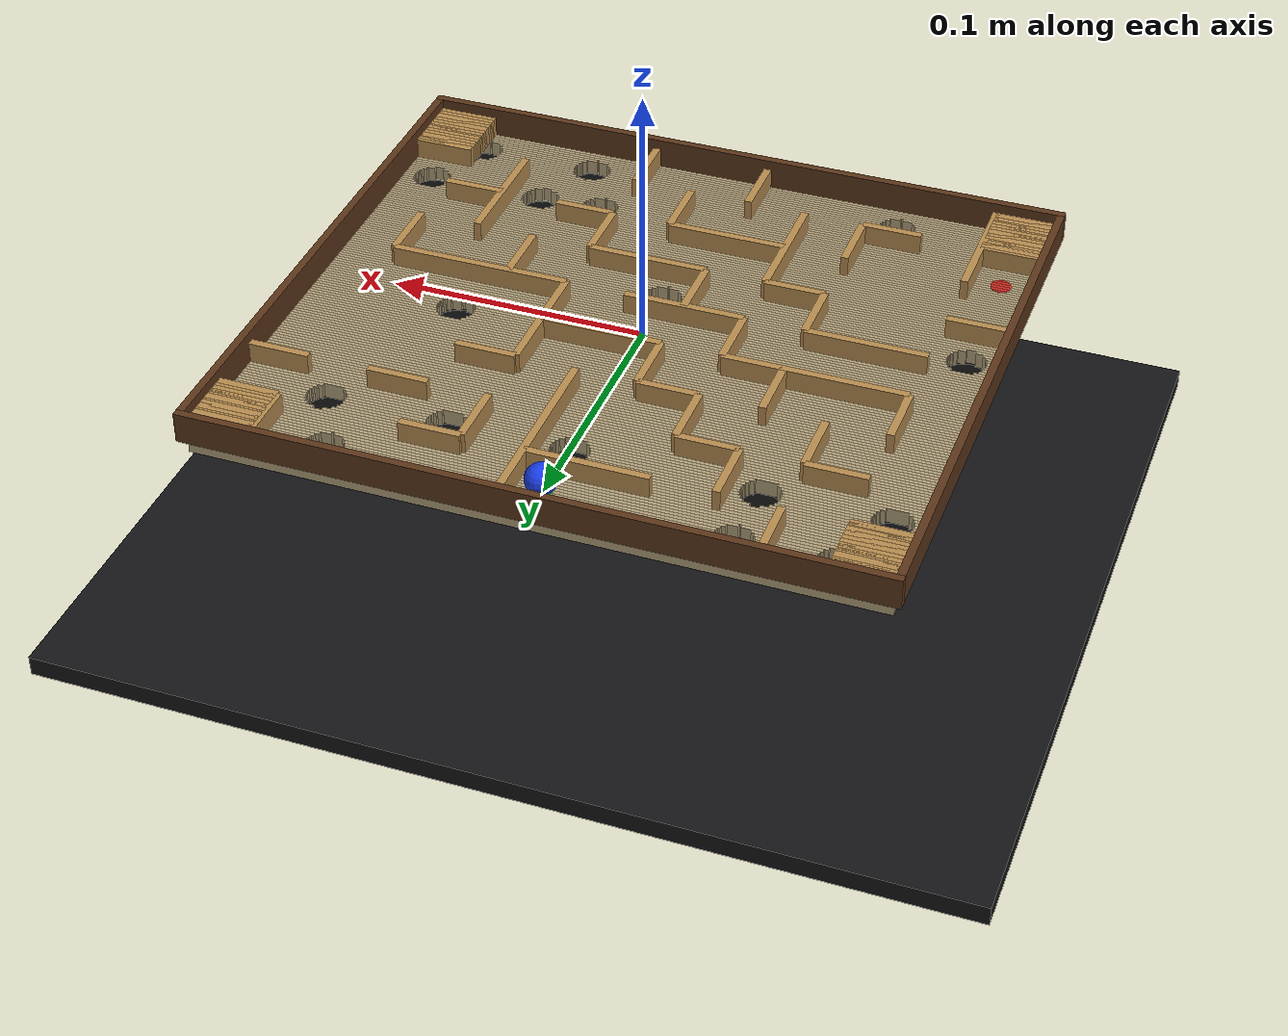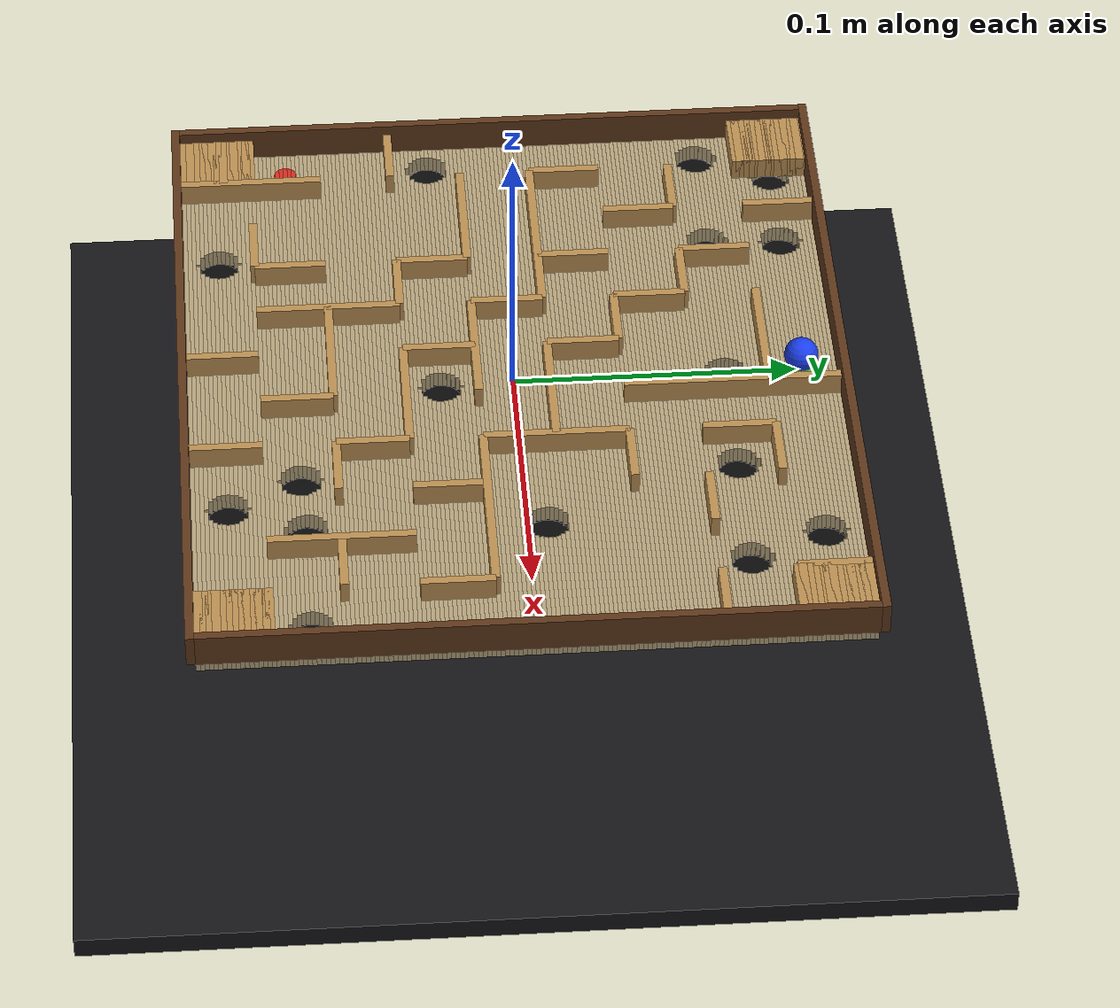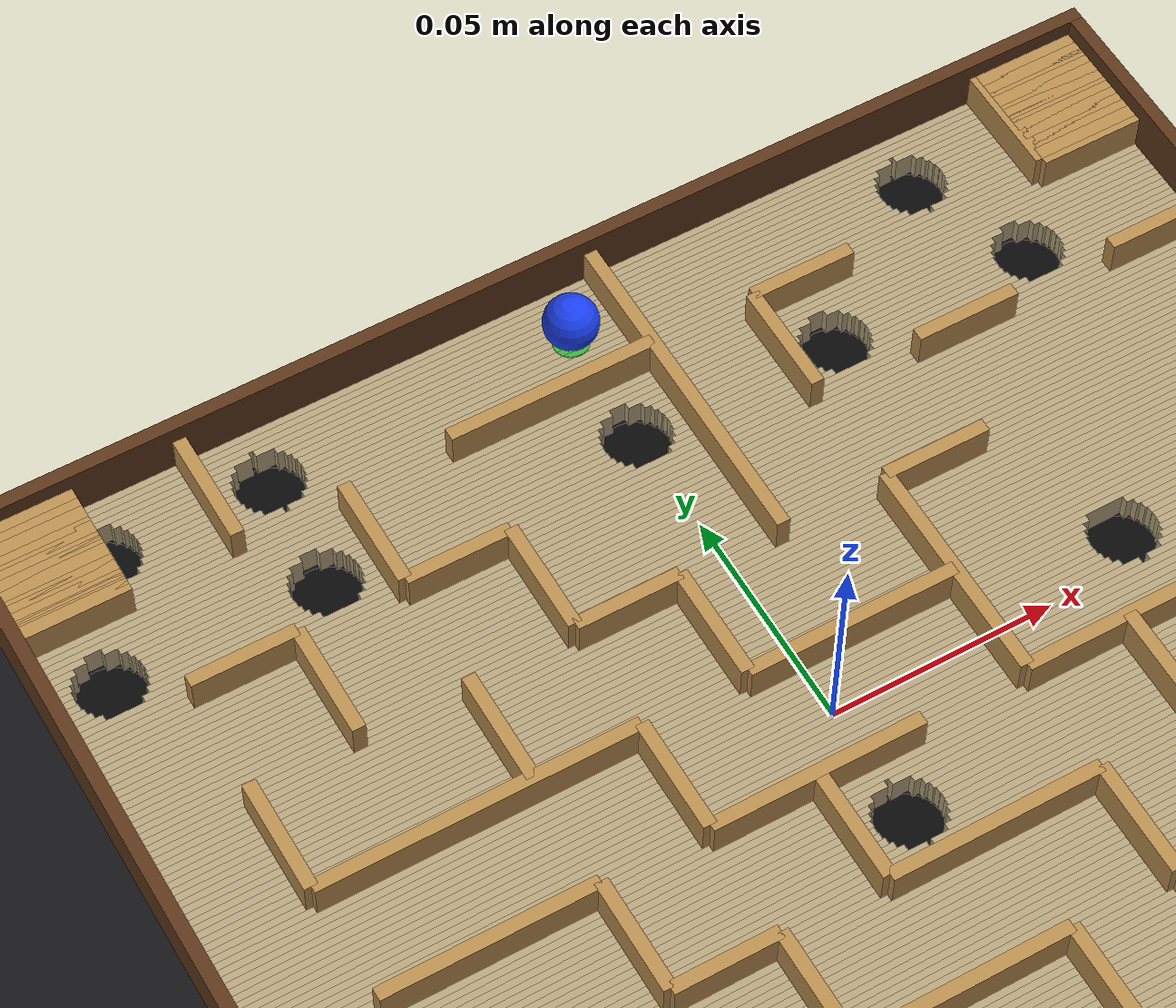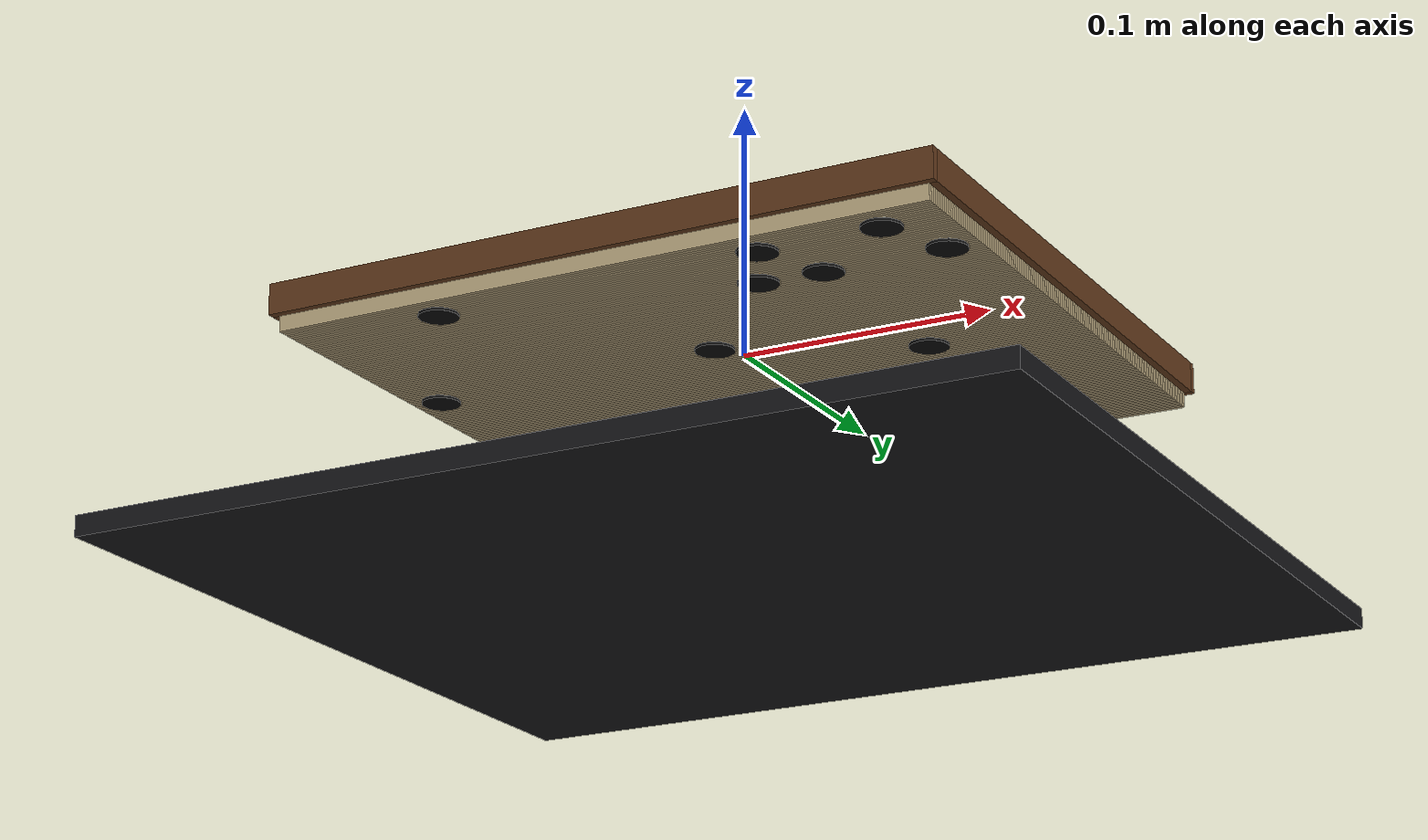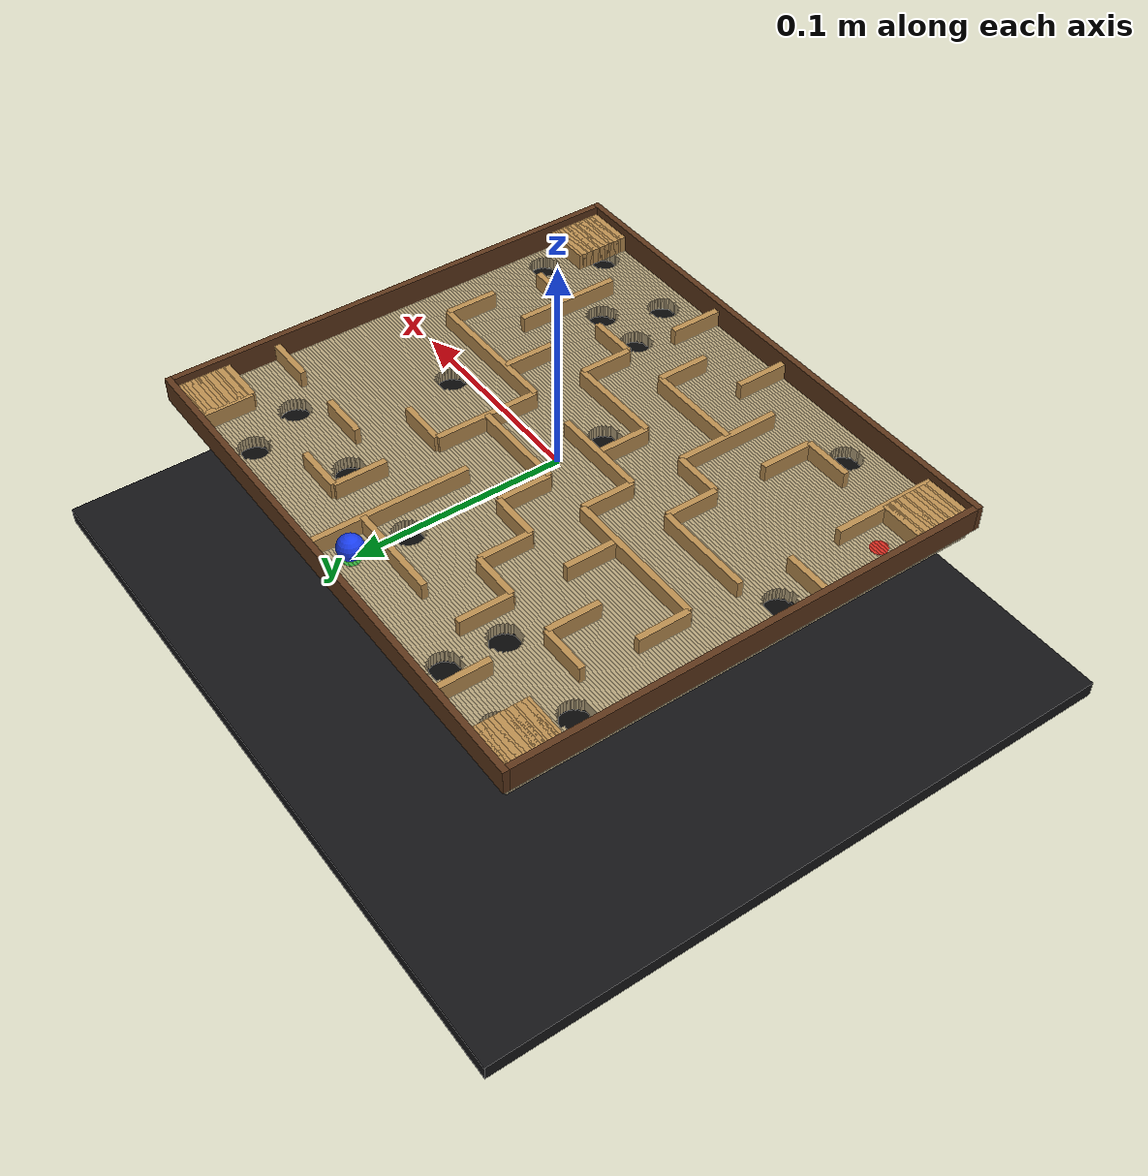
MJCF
<mujoco model="tag_custom_maze">
  <compiler angle="radian" inertiafromgeom="auto"/>
  <option timestep="0.001" gravity="0 0 -9.81" integrator="implicitfast" solver="Newton" iterations="12" tolerance="1e-9"/>
  <size nconmax="4000" njmax="12000"/>
  <visual>
    <global offwidth="900" offheight="800"/>
    <quality shadowsize="2048"/>
    <map znear="0.01" zfar="3"/>
  </visual>
  <default>
    <default class="floor">
      <geom condim="6" friction="0.3 0.015 0.002" solref="0.004 1" solimp="0.95 0.99 0.001" density="650"/>
    </default>
    <default class="wall">
      <geom condim="6" friction="0.35 0.02 0.003" solref="0.003 1" solimp="0.95 0.99 0.001" density="700"/>
    </default>
  </default>
  <worldbody>
    <light name="key" pos="0 -0.15 0.55" dir="0 0 -1" diffuse="0.9 0.9 0.9"/>
    <light name="fill" pos="-0.25 0.2 0.35" dir="0.4 -0.3 -1" diffuse="0.45 0.45 0.45"/>
    <camera name="top" pos="0 0 0.43" quat="1 0 0 0" mode="fixed" fovy="37"/>
    <geom name="catch_tray" type="box" pos="0 0 -0.085" size="0.18 0.16 0.004" rgba="0.08 0.08 0.09 1" friction="0.5 0.02 0.003"/>
    <body name="tilt_x_frame" pos="0 0 0">
      <inertial pos="0 0 0" mass="0.02" diaginertia="0.0001 0.0001 0.0001"/>
      <joint name="tilt_x" type="hinge" axis="1 0 0" range="-0.20943951 0.20943951" damping="0.8" armature="0.01"/>
      <body name="board" pos="0 0 0">
        <joint name="tilt_y" type="hinge" axis="0 1 0" range="-0.20943951 0.20943951" damping="0.8" armature="0.01"/>
        <geom name="floor_0" type="box" pos="0 -0.113751634 -0.003" size="0.1295 0.000748366013 0.003" rgba="0.70 0.63 0.48 1" class="floor"/><geom name="floor_1" type="box" pos="0 -0.112254902 -0.003" size="0.1295 0.000748366013 0.003" rgba="0.70 0.63 0.48 1" class="floor"/><geom name="floor_2" type="box" pos="0 -0.11075817 -0.003" size="0.1295 0.000748366013 0.003" rgba="0.70 0.63 0.48 1" class="floor"/><geom name="floor_3" type="box" pos="-0.0997269475 -0.109261438 -0.003" size="0.0297730525 0.000748366013 0.003" rgba="0.70 0.63 0.48 1" class="floor"/><geom name="floor_4" type="box" pos="-0.00529772727 -0.109261438 -0.003" size="0.0636665596 0.000748366013 0.003" rgba="0.70 0.63 0.48 1" class="floor"/><geom name="floor_5" type="box" pos="0.0824090909 -0.109261438 -0.003" size="0.0230506505 0.000748366013 0.003" rgba="0.70 0.63 0.48 1" class="floor"/><geom name="floor_6" type="box" pos="0.117974675 -0.109261438 -0.003" size="0.0115253252 0.000748366013 0.003" rgba="0.70 0.63 0.48 1" class="floor"/><geom name="floor_7" type="box" pos="-0.101738234 -0.107764706 -0.003" size="0.0277617662 0.000748366013 0.003" rgba="0.70 0.63 0.48 1" class="floor"/><geom name="floor_8" type="box" pos="-0.00529772727 -0.107764706 -0.003" size="0.059643987 0.000748366013 0.003" rgba="0.70 0.63 0.48 1" class="floor"/><geom name="floor_9" type="box" pos="0.0824090909 -0.107764706 -0.003" size="0.0190280779 0.000748366013 0.003" rgba="0.70 0.63 0.48 1" class="floor"/><geom name="floor_10" type="box" pos="0.119985961 -0.107764706 -0.003" size="0.00951403894 0.000748366013 0.003" rgba="0.70 0.63 0.48 1" class="floor"/><geom name="floor_11" type="box" pos="-0.102483216 -0.106267974 -0.003" size="0.0270167843 0.000748366013 0.003" rgba="0.70 0.63 0.48 1" class="floor"/><geom name="floor_12" type="box" pos="-0.00529772727 -0.106267974 -0.003" size="0.0581540232 0.000748366013 0.003" rgba="0.70 0.63 0.48 1" class="floor"/><geom name="floor_13" type="box" pos="0.0824090909 -0.106267974 -0.003" size="0.0175381141 0.000748366013 0.003" rgba="0.70 0.63 0.48 1" class="floor"/><geom name="floor_14" type="box" pos="0.120730943 -0.106267974 -0.003" size="0.00876905705 0.000748366013 0.003" rgba="0.70 0.63 0.48 1" class="floor"/><geom name="floor_15" type="box" pos="-0.102917902 -0.104771242 -0.003" size="0.0265820984 0.000748366013 0.003" rgba="0.70 0.63 0.48 1" class="floor"/><geom name="floor_16" type="box" pos="-0.00529772727 -0.104771242 -0.003" size="0.0572846513 0.000748366013 0.003" rgba="0.70 0.63 0.48 1" class="floor"/><geom name="floor_17" type="box" pos="0.0824090909 -0.104771242 -0.003" size="0.0166687422 0.000748366013 0.003" rgba="0.70 0.63 0.48 1" class="floor"/><geom name="floor_18" type="box" pos="0.121165629 -0.104771242 -0.003" size="0.00833437109 0.000748366013 0.003" rgba="0.70 0.63 0.48 1" class="floor"/><geom name="floor_19" type="box" pos="-0.103154113 -0.10327451 -0.003" size="0.0263458868 0.000748366013 0.003" rgba="0.70 0.63 0.48 1" class="floor"/><geom name="floor_20" type="box" pos="-0.00529772727 -0.10327451 -0.003" size="0.0568122281 0.000748366013 0.003" rgba="0.70 0.63 0.48 1" class="floor"/><geom name="floor_21" type="box" pos="0.0824090909 -0.10327451 -0.003" size="0.016196319 0.000748366013 0.003" rgba="0.70 0.63 0.48 1" class="floor"/><geom name="floor_22" type="box" pos="0.12140184 -0.10327451 -0.003" size="0.0080981595 0.000748366013 0.003" rgba="0.70 0.63 0.48 1" class="floor"/><geom name="floor_23" type="box" pos="-0.103229545 -0.101777778 -0.003" size="0.0262704545 0.000748366013 0.003" rgba="0.70 0.63 0.48 1" class="floor"/><geom name="floor_24" type="box" pos="-0.00529772727 -0.101777778 -0.003" size="0.0566613636 0.000748366013 0.003" rgba="0.70 0.63 0.48 1" class="floor"/><geom name="floor_25" type="box" pos="0.0824090909 -0.101777778 -0.003" size="0.0160454545 0.000748366013 0.003" rgba="0.70 0.63 0.48 1" class="floor"/><geom name="floor_26" type="box" pos="0.121477273 -0.101777778 -0.003" size="0.00802272727 0.000748366013 0.003" rgba="0.70 0.63 0.48 1" class="floor"/><geom name="floor_27" type="box" pos="-0.103154113 -0.100281046 -0.003" size="0.0263458868 0.000748366013 0.003" rgba="0.70 0.63 0.48 1" class="floor"/><geom name="floor_28" type="box" pos="-0.00529772727 -0.100281046 -0.003" size="0.0568122281 0.000748366013 0.003" rgba="0.70 0.63 0.48 1" class="floor"/><geom name="floor_29" type="box" pos="0.0824090909 -0.100281046 -0.003" size="0.016196319 0.000748366013 0.003" rgba="0.70 0.63 0.48 1" class="floor"/><geom name="floor_30" type="box" pos="0.12140184 -0.100281046 -0.003" size="0.0080981595 0.000748366013 0.003" rgba="0.70 0.63 0.48 1" class="floor"/><geom name="floor_31" type="box" pos="-0.102917902 -0.0987843137 -0.003" size="0.0265820984 0.000748366013 0.003" rgba="0.70 0.63 0.48 1" class="floor"/><geom name="floor_32" type="box" pos="-0.00529772727 -0.0987843137 -0.003" size="0.0572846513 0.000748366013 0.003" rgba="0.70 0.63 0.48 1" class="floor"/><geom name="floor_33" type="box" pos="0.0824090909 -0.0987843137 -0.003" size="0.0166687422 0.000748366013 0.003" rgba="0.70 0.63 0.48 1" class="floor"/><geom name="floor_34" type="box" pos="0.121165629 -0.0987843137 -0.003" size="0.00833437109 0.000748366013 0.003" rgba="0.70 0.63 0.48 1" class="floor"/><geom name="floor_35" type="box" pos="-0.102483216 -0.0972875817 -0.003" size="0.0270167843 0.000748366013 0.003" rgba="0.70 0.63 0.48 1" class="floor"/><geom name="floor_36" type="box" pos="-0.00529772727 -0.0972875817 -0.003" size="0.0581540232 0.000748366013 0.003" rgba="0.70 0.63 0.48 1" class="floor"/><geom name="floor_37" type="box" pos="0.0824090909 -0.0972875817 -0.003" size="0.0175381141 0.000748366013 0.003" rgba="0.70 0.63 0.48 1" class="floor"/><geom name="floor_38" type="box" pos="0.120730943 -0.0972875817 -0.003" size="0.00876905705 0.000748366013 0.003" rgba="0.70 0.63 0.48 1" class="floor"/><geom name="floor_39" type="box" pos="-0.101738234 -0.0957908497 -0.003" size="0.0277617662 0.000748366013 0.003" rgba="0.70 0.63 0.48 1" class="floor"/><geom name="floor_40" type="box" pos="-0.00529772727 -0.0957908497 -0.003" size="0.059643987 0.000748366013 0.003" rgba="0.70 0.63 0.48 1" class="floor"/><geom name="floor_41" type="box" pos="0.0824090909 -0.0957908497 -0.003" size="0.0190280779 0.000748366013 0.003" rgba="0.70 0.63 0.48 1" class="floor"/><geom name="floor_42" type="box" pos="0.119985961 -0.0957908497 -0.003" size="0.00951403894 0.000748366013 0.003" rgba="0.70 0.63 0.48 1" class="floor"/><geom name="floor_43" type="box" pos="-0.0997269475 -0.0942941176 -0.003" size="0.0297730525 0.000748366013 0.003" rgba="0.70 0.63 0.48 1" class="floor"/><geom name="floor_44" type="box" pos="-0.00529772727 -0.0942941176 -0.003" size="0.0636665596 0.000748366013 0.003" rgba="0.70 0.63 0.48 1" class="floor"/><geom name="floor_45" type="box" pos="0.0824090909 -0.0942941176 -0.003" size="0.0230506505 0.000748366013 0.003" rgba="0.70 0.63 0.48 1" class="floor"/><geom name="floor_46" type="box" pos="0.117974675 -0.0942941176 -0.003" size="0.0115253252 0.000748366013 0.003" rgba="0.70 0.63 0.48 1" class="floor"/><geom name="floor_47" type="box" pos="0 -0.0927973856 -0.003" size="0.1295 0.000748366013 0.003" rgba="0.70 0.63 0.48 1" class="floor"/><geom name="floor_48" type="box" pos="0 -0.0913006536 -0.003" size="0.1295 0.000748366013 0.003" rgba="0.70 0.63 0.48 1" class="floor"/><geom name="floor_49" type="box" pos="0 -0.0898039216 -0.003" size="0.1295 0.000748366013 0.003" rgba="0.70 0.63 0.48 1" class="floor"/><geom name="floor_50" type="box" pos="0 -0.0883071895 -0.003" size="0.1295 0.000748366013 0.003" rgba="0.70 0.63 0.48 1" class="floor"/><geom name="floor_51" type="box" pos="0 -0.0868104575 -0.003" size="0.1295 0.000748366013 0.003" rgba="0.70 0.63 0.48 1" class="floor"/><geom name="floor_52" type="box" pos="0 -0.0853137255 -0.003" size="0.1295 0.000748366013 0.003" rgba="0.70 0.63 0.48 1" class="floor"/><geom name="floor_53" type="box" pos="-0.0420405838 -0.0838169935 -0.003" size="0.0874594162 0.000748366013 0.003" rgba="0.70 0.63 0.48 1" class="floor"/><geom name="floor_54" type="box" pos="0.0879542202 -0.0838169935 -0.003" size="0.0415457798 0.000748366013 0.003" rgba="0.70 0.63 0.48 1" class="floor"/><geom name="floor_55" type="box" pos="-0.0440518701 -0.0823202614 -0.003" size="0.0854481299 0.000748366013 0.003" rgba="0.70 0.63 0.48 1" class="floor"/><geom name="floor_56" type="box" pos="0.0595909879 -0.0823202614 -0.003" size="0.00915997486 0.000748366013 0.003" rgba="0.70 0.63 0.48 1" class="floor"/><geom name="floor_57" type="box" pos="0.0941818182 -0.0823202614 -0.003" size="0.0216600537 0.000748366013 0.003" rgba="0.70 0.63 0.48 1" class="floor"/><geom name="floor_58" type="box" pos="0.124556337 -0.0823202614 -0.003" size="0.00494366319 0.000748366013 0.003" rgba="0.70 0.63 0.48 1" class="floor"/><geom name="floor_59" type="box" pos="-0.044796852 -0.0808235294 -0.003" size="0.084703148 0.000748366013 0.003" rgba="0.70 0.63 0.48 1" class="floor"/><geom name="floor_60" type="box" pos="0.058878434 -0.0808235294 -0.003" size="0.00695745721 0.000748366013 0.003" rgba="0.70 0.63 0.48 1" class="floor"/><geom name="floor_61" type="box" pos="0.0941818182 -0.0808235294 -0.003" size="0.0187449821 0.000748366013 0.003" rgba="0.70 0.63 0.48 1" class="floor"/><geom name="floor_62" type="box" pos="0.126013873 -0.0808235294 -0.003" size="0.00348612743 0.000748366013 0.003" rgba="0.70 0.63 0.48 1" class="floor"/><geom name="floor_63" type="box" pos="-0.045231538 -0.0793267974 -0.003" size="0.084268462 0.000748366013 0.003" rgba="0.70 0.63 0.48 1" class="floor"/><geom name="floor_64" type="box" pos="0.0586289632 -0.0793267974 -0.003" size="0.00583861446 0.000748366013 0.003" rgba="0.70 0.63 0.48 1" class="floor"/><geom name="floor_65" type="box" pos="0.0941818182 -0.0793267974 -0.003" size="0.0173766686 0.000748366013 0.003" rgba="0.70 0.63 0.48 1" class="floor"/><geom name="floor_66" type="box" pos="0.126698029 -0.0793267974 -0.003" size="0.00280197064 0.000748366013 0.003" rgba="0.70 0.63 0.48 1" class="floor"/><geom name="floor_67" type="box" pos="-0.0454677496 -0.0778300654 -0.003" size="0.0840322504 0.000748366013 0.003" rgba="0.70 0.63 0.48 1" class="floor"/><geom name="floor_68" type="box" pos="0.0584644963 -0.0778300654 -0.003" size="0.0052017244 0.000748366013 0.003" rgba="0.70 0.63 0.48 1" class="floor"/><geom name="floor_69" type="box" pos="0.0941818182 -0.0778300654 -0.003" size="0.0165753116 0.000748366013 0.003" rgba="0.70 0.63 0.48 1" class="floor"/><geom name="floor_70" type="box" pos="0.127098708 -0.0778300654 -0.003" size="0.00240129217 0.000748366013 0.003" rgba="0.70 0.63 0.48 1" class="floor"/><geom name="floor_71" type="box" pos="-0.0455431818 -0.0763333333 -0.003" size="0.0839568182 0.000748366013 0.003" rgba="0.70 0.63 0.48 1" class="floor"/><geom name="floor_72" type="box" pos="0.0583293454 -0.0763333333 -0.003" size="0.00491570907 0.000748366013 0.003" rgba="0.70 0.63 0.48 1" class="floor"/><geom name="floor_73" type="box" pos="0.0941818182 -0.0763333333 -0.003" size="0.0161541454 0.000748366013 0.003" rgba="0.70 0.63 0.48 1" class="floor"/><geom name="floor_74" type="box" pos="0.127309291 -0.0763333333 -0.003" size="0.00219070907 0.000748366013 0.003" rgba="0.70 0.63 0.48 1" class="floor"/><geom name="floor_75" type="box" pos="-0.0454677496 -0.0748366013 -0.003" size="0.0840322504 0.000748366013 0.003" rgba="0.70 0.63 0.48 1" class="floor"/><geom name="floor_76" type="box" pos="0.0582012483 -0.0748366013 -0.003" size="0.0049384764 0.000748366013 0.003" rgba="0.70 0.63 0.48 1" class="floor"/><geom name="floor_77" type="box" pos="0.0941818182 -0.0748366013 -0.003" size="0.0160488156 0.000748366013 0.003" rgba="0.70 0.63 0.48 1" class="floor"/><geom name="floor_78" type="box" pos="0.127361956 -0.0748366013 -0.003" size="0.00213804417 0.000748366013 0.003" rgba="0.70 0.63 0.48 1" class="floor"/><geom name="floor_79" type="box" pos="-0.045231538 -0.0733398693 -0.003" size="0.084268462 0.000748366013 0.003" rgba="0.70 0.63 0.48 1" class="floor"/><geom name="floor_80" type="box" pos="0.0580634477 -0.0733398693 -0.003" size="0.00527309901 0.000748366013 0.003" rgba="0.70 0.63 0.48 1" class="floor"/><geom name="floor_81" type="box" pos="0.0941818182 -0.0733398693 -0.003" size="0.0162456377 0.000748366013 0.003" rgba="0.70 0.63 0.48 1" class="floor"/><geom name="floor_82" type="box" pos="0.127263545 -0.0733398693 -0.003" size="0.00223645519 0.000748366013 0.003" rgba="0.70 0.63 0.48 1" class="floor"/><geom name="floor_83" type="box" pos="-0.044796852 -0.0718431373 -0.003" size="0.084703148 0.000748366013 0.003" rgba="0.70 0.63 0.48 1" class="floor"/><geom name="floor_84" type="box" pos="0.0578913909 -0.0718431373 -0.003" size="0.00597041411 0.000748366013 0.003" rgba="0.70 0.63 0.48 1" class="floor"/><geom name="floor_85" type="box" pos="0.0941818182 -0.0718431373 -0.003" size="0.0167708959 0.000748366013 0.003" rgba="0.70 0.63 0.48 1" class="floor"/><geom name="floor_86" type="box" pos="0.127000916 -0.0718431373 -0.003" size="0.00249908434 0.000748366013 0.003" rgba="0.70 0.63 0.48 1" class="floor"/><geom name="floor_87" type="box" pos="-0.0440518701 -0.0703464052 -0.003" size="0.0854481299 0.000748366013 0.003" rgba="0.70 0.63 0.48 1" class="floor"/><geom name="floor_88" type="box" pos="0.0576172886 -0.0703464052 -0.003" size="0.00718627562 0.000748366013 0.003" rgba="0.70 0.63 0.48 1" class="floor"/><geom name="floor_89" type="box" pos="0.0941818182 -0.0703464052 -0.003" size="0.0177126552 0.000748366013 0.003" rgba="0.70 0.63 0.48 1" class="floor"/><geom name="floor_90" type="box" pos="0.126530036 -0.0703464052 -0.003" size="0.00296996395 0.000748366013 0.003" rgba="0.70 0.63 0.48 1" class="floor"/><geom name="floor_91" type="box" pos="-0.0420405838 -0.0688496732 -0.003" size="0.0874594162 0.000748366013 0.003" rgba="0.70 0.63 0.48 1" class="floor"/><geom name="floor_92" type="box" pos="0.0564207337 -0.0688496732 -0.003" size="0.0100122933 0.000748366013 0.003" rgba="0.70 0.63 0.48 1" class="floor"/><geom name="floor_93" type="box" pos="0.0941818182 -0.0688496732 -0.003" size="0.0193421179 0.000748366013 0.003" rgba="0.70 0.63 0.48 1" class="floor"/><geom name="floor_94" type="box" pos="0.125715305 -0.0688496732 -0.003" size="0.0037846953 0.000748366013 0.003" rgba="0.70 0.63 0.48 1" class="floor"/><geom name="floor_95" type="box" pos="0 -0.0673529412 -0.003" size="0.1295 0.000748366013 0.003" rgba="0.70 0.63 0.48 1" class="floor"/><geom name="floor_96" type="box" pos="0 -0.0658562092 -0.003" size="0.1295 0.000748366013 0.003" rgba="0.70 0.63 0.48 1" class="floor"/><geom name="floor_97" type="box" pos="0 -0.0643594771 -0.003" size="0.1295 0.000748366013 0.003" rgba="0.70 0.63 0.48 1" class="floor"/><geom name="floor_98" type="box" pos="0 -0.0628627451 -0.003" size="0.1295 0.000748366013 0.003" rgba="0.70 0.63 0.48 1" class="floor"/><geom name="floor_99" type="box" pos="0 -0.0613660131 -0.003" size="0.1295 0.000748366013 0.003" rgba="0.70 0.63 0.48 1" class="floor"/><geom name="floor_100" type="box" pos="0 -0.059869281 -0.003" size="0.1295 0.000748366013 0.003" rgba="0.70 0.63 0.48 1" class="floor"/><geom name="floor_101" type="box" pos="0 -0.058372549 -0.003" size="0.1295 0.000748366013 0.003" rgba="0.70 0.63 0.48 1" class="floor"/><geom name="floor_102" type="box" pos="0 -0.056875817 -0.003" size="0.1295 0.000748366013 0.003" rgba="0.70 0.63 0.48 1" class="floor"/><geom name="floor_103" type="box" pos="0 -0.055379085 -0.003" size="0.1295 0.000748366013 0.003" rgba="0.70 0.63 0.48 1" class="floor"/><geom name="floor_104" type="box" pos="0 -0.0538823529 -0.003" size="0.1295 0.000748366013 0.003" rgba="0.70 0.63 0.48 1" class="floor"/><geom name="floor_105" type="box" pos="0 -0.0523856209 -0.003" size="0.1295 0.000748366013 0.003" rgba="0.70 0.63 0.48 1" class="floor"/><geom name="floor_106" type="box" pos="0 -0.0508888889 -0.003" size="0.1295 0.000748366013 0.003" rgba="0.70 0.63 0.48 1" class="floor"/><geom name="floor_107" type="box" pos="0 -0.0493921569 -0.003" size="0.1295 0.000748366013 0.003" rgba="0.70 0.63 0.48 1" class="floor"/><geom name="floor_108" type="box" pos="0 -0.0478954248 -0.003" size="0.1295 0.000748366013 0.003" rgba="0.70 0.63 0.48 1" class="floor"/><geom name="floor_109" type="box" pos="0 -0.0463986928 -0.003" size="0.1295 0.000748366013 0.003" rgba="0.70 0.63 0.48 1" class="floor"/><geom name="floor_110" type="box" pos="0 -0.0449019608 -0.003" size="0.1295 0.000748366013 0.003" rgba="0.70 0.63 0.48 1" class="floor"/><geom name="floor_111" type="box" pos="0 -0.0434052288 -0.003" size="0.1295 0.000748366013 0.003" rgba="0.70 0.63 0.48 1" class="floor"/><geom name="floor_112" type="box" pos="0 -0.0419084967 -0.003" size="0.1295 0.000748366013 0.003" rgba="0.70 0.63 0.48 1" class="floor"/><geom name="floor_113" type="box" pos="0 -0.0404117647 -0.003" size="0.1295 0.000748366013 0.003" rgba="0.70 0.63 0.48 1" class="floor"/><geom name="floor_114" type="box" pos="0 -0.0389150327 -0.003" size="0.1295 0.000748366013 0.003" rgba="0.70 0.63 0.48 1" class="floor"/><geom name="floor_115" type="box" pos="0 -0.0374183007 -0.003" size="0.1295 0.000748366013 0.003" rgba="0.70 0.63 0.48 1" class="floor"/><geom name="floor_116" type="box" pos="0 -0.0359215686 -0.003" size="0.1295 0.000748366013 0.003" rgba="0.70 0.63 0.48 1" class="floor"/><geom name="floor_117" type="box" pos="0 -0.0344248366 -0.003" size="0.1295 0.000748366013 0.003" rgba="0.70 0.63 0.48 1" class="floor"/><geom name="floor_118" type="box" pos="-0.0644087657 -0.0329281046 -0.003" size="0.0650912343 0.000748366013 0.003" rgba="0.70 0.63 0.48 1" class="floor"/><geom name="floor_119" type="box" pos="0.0655860384 -0.0329281046 -0.003" size="0.0639139616 0.000748366013 0.003" rgba="0.70 0.63 0.48 1" class="floor"/><geom name="floor_120" type="box" pos="-0.124556337 -0.0314313725 -0.003" size="0.00494366319 0.000748366013 0.003" rgba="0.70 0.63 0.48 1" class="floor"/><geom name="floor_121" type="box" pos="-0.0595909879 -0.0314313725 -0.003" size="0.056250884 0.000748366013 0.003" rgba="0.70 0.63 0.48 1" class="floor"/><geom name="floor_122" type="box" pos="0.0675973247 -0.0314313725 -0.003" size="0.0619026753 0.000748366013 0.003" rgba="0.70 0.63 0.48 1" class="floor"/><geom name="floor_123" type="box" pos="-0.126013873 -0.0299346405 -0.003" size="0.00348612743 0.000748366013 0.003" rgba="0.70 0.63 0.48 1" class="floor"/><geom name="floor_124" type="box" pos="-0.058878434 -0.0299346405 -0.003" size="0.0540483663 0.000748366013 0.003" rgba="0.70 0.63 0.48 1" class="floor"/><geom name="floor_125" type="box" pos="0.0683423066 -0.0299346405 -0.003" size="0.0611576934 0.000748366013 0.003" rgba="0.70 0.63 0.48 1" class="floor"/><geom name="floor_126" type="box" pos="-0.126698029 -0.0284379085 -0.003" size="0.00280197064 0.000748366013 0.003" rgba="0.70 0.63 0.48 1" class="floor"/><geom name="floor_127" type="box" pos="-0.0586289632 -0.0284379085 -0.003" size="0.0529295235 0.000748366013 0.003" rgba="0.70 0.63 0.48 1" class="floor"/><geom name="floor_128" type="box" pos="0.0687769925 -0.0284379085 -0.003" size="0.0607230075 0.000748366013 0.003" rgba="0.70 0.63 0.48 1" class="floor"/><geom name="floor_129" type="box" pos="-0.127098708 -0.0269411765 -0.003" size="0.00240129217 0.000748366013 0.003" rgba="0.70 0.63 0.48 1" class="floor"/><geom name="floor_130" type="box" pos="-0.0584644963 -0.0269411765 -0.003" size="0.0522926335 0.000748366013 0.003" rgba="0.70 0.63 0.48 1" class="floor"/><geom name="floor_131" type="box" pos="0.0690132041 -0.0269411765 -0.003" size="0.0604867959 0.000748366013 0.003" rgba="0.70 0.63 0.48 1" class="floor"/><geom name="floor_132" type="box" pos="-0.127309291 -0.0254444444 -0.003" size="0.00219070907 0.000748366013 0.003" rgba="0.70 0.63 0.48 1" class="floor"/><geom name="floor_133" type="box" pos="-0.0583293454 -0.0254444444 -0.003" size="0.0520066182 0.000748366013 0.003" rgba="0.70 0.63 0.48 1" class="floor"/><geom name="floor_134" type="box" pos="0.0690886364 -0.0254444444 -0.003" size="0.0604113636 0.000748366013 0.003" rgba="0.70 0.63 0.48 1" class="floor"/><geom name="floor_135" type="box" pos="-0.127361956 -0.0239477124 -0.003" size="0.00213804417 0.000748366013 0.003" rgba="0.70 0.63 0.48 1" class="floor"/><geom name="floor_136" type="box" pos="-0.0582012483 -0.0239477124 -0.003" size="0.0520293855 0.000748366013 0.003" rgba="0.70 0.63 0.48 1" class="floor"/><geom name="floor_137" type="box" pos="0.0690132041 -0.0239477124 -0.003" size="0.0604867959 0.000748366013 0.003" rgba="0.70 0.63 0.48 1" class="floor"/><geom name="floor_138" type="box" pos="-0.127263545 -0.0224509804 -0.003" size="0.00223645519 0.000748366013 0.003" rgba="0.70 0.63 0.48 1" class="floor"/><geom name="floor_139" type="box" pos="-0.0580634477 -0.0224509804 -0.003" size="0.0523640081 0.000748366013 0.003" rgba="0.70 0.63 0.48 1" class="floor"/><geom name="floor_140" type="box" pos="0.0687769925 -0.0224509804 -0.003" size="0.0607230075 0.000748366013 0.003" rgba="0.70 0.63 0.48 1" class="floor"/><geom name="floor_141" type="box" pos="-0.127000916 -0.0209542484 -0.003" size="0.00249908434 0.000748366013 0.003" rgba="0.70 0.63 0.48 1" class="floor"/><geom name="floor_142" type="box" pos="-0.0578913909 -0.0209542484 -0.003" size="0.0530613232 0.000748366013 0.003" rgba="0.70 0.63 0.48 1" class="floor"/><geom name="floor_143" type="box" pos="0.0683423066 -0.0209542484 -0.003" size="0.0611576934 0.000748366013 0.003" rgba="0.70 0.63 0.48 1" class="floor"/><geom name="floor_144" type="box" pos="-0.126530036 -0.0194575163 -0.003" size="0.00296996395 0.000748366013 0.003" rgba="0.70 0.63 0.48 1" class="floor"/><geom name="floor_145" type="box" pos="-0.0576172886 -0.0194575163 -0.003" size="0.0542771847 0.000748366013 0.003" rgba="0.70 0.63 0.48 1" class="floor"/><geom name="floor_146" type="box" pos="0.0675973247 -0.0194575163 -0.003" size="0.0619026753 0.000748366013 0.003" rgba="0.70 0.63 0.48 1" class="floor"/><geom name="floor_147" type="box" pos="-0.125715305 -0.0179607843 -0.003" size="0.0037846953 0.000748366013 0.003" rgba="0.70 0.63 0.48 1" class="floor"/><geom name="floor_148" type="box" pos="-0.0564207337 -0.0179607843 -0.003" size="0.0571032024 0.000748366013 0.003" rgba="0.70 0.63 0.48 1" class="floor"/><geom name="floor_149" type="box" pos="0.0655860384 -0.0179607843 -0.003" size="0.0639139616 0.000748366013 0.003" rgba="0.70 0.63 0.48 1" class="floor"/><geom name="floor_150" type="box" pos="0 -0.0164640523 -0.003" size="0.1295 0.000748366013 0.003" rgba="0.70 0.63 0.48 1" class="floor"/><geom name="floor_151" type="box" pos="0 -0.0149673203 -0.003" size="0.1295 0.000748366013 0.003" rgba="0.70 0.63 0.48 1" class="floor"/><geom name="floor_152" type="box" pos="0 -0.0134705882 -0.003" size="0.1295 0.000748366013 0.003" rgba="0.70 0.63 0.48 1" class="floor"/><geom name="floor_153" type="box" pos="0 -0.0119738562 -0.003" size="0.1295 0.000748366013 0.003" rgba="0.70 0.63 0.48 1" class="floor"/><geom name="floor_154" type="box" pos="0 -0.0104771242 -0.003" size="0.1295 0.000748366013 0.003" rgba="0.70 0.63 0.48 1" class="floor"/><geom name="floor_155" type="box" pos="0 -0.00898039216 -0.003" size="0.1295 0.000748366013 0.003" rgba="0.70 0.63 0.48 1" class="floor"/><geom name="floor_156" type="box" pos="0 -0.00748366013 -0.003" size="0.1295 0.000748366013 0.003" rgba="0.70 0.63 0.48 1" class="floor"/><geom name="floor_157" type="box" pos="0 -0.0059869281 -0.003" size="0.1295 0.000748366013 0.003" rgba="0.70 0.63 0.48 1" class="floor"/><geom name="floor_158" type="box" pos="0 -0.00449019608 -0.003" size="0.1295 0.000748366013 0.003" rgba="0.70 0.63 0.48 1" class="floor"/><geom name="floor_159" type="box" pos="0 -0.00299346405 -0.003" size="0.1295 0.000748366013 0.003" rgba="0.70 0.63 0.48 1" class="floor"/><geom name="floor_160" type="box" pos="0 -0.00149673203 -0.003" size="0.1295 0.000748366013 0.003" rgba="0.70 0.63 0.48 1" class="floor"/><geom name="floor_161" type="box" pos="-0.0291146803 -1.38777878e-17 -0.003" size="0.10038532 0.000748366013 0.003" rgba="0.70 0.63 0.48 1" class="floor"/><geom name="floor_162" type="box" pos="0.101296499 -1.38777878e-17 -0.003" size="0.0282035015 0.000748366013 0.003" rgba="0.70 0.63 0.48 1" class="floor"/><geom name="floor_163" type="box" pos="-0.0309435338 0.00149673203 -0.003" size="0.0985564662 0.000748366013 0.003" rgba="0.70 0.63 0.48 1" class="floor"/><geom name="floor_164" type="box" pos="0.103125352 0.00149673203 -0.003" size="0.026374648 0.000748366013 0.003" rgba="0.70 0.63 0.48 1" class="floor"/><geom name="floor_165" type="box" pos="-0.0316773178 0.00299346405 -0.003" size="0.0978226822 0.000748366013 0.003" rgba="0.70 0.63 0.48 1" class="floor"/><geom name="floor_166" type="box" pos="0.103859136 0.00299346405 -0.003" size="0.025640864 0.000748366013 0.003" rgba="0.70 0.63 0.48 1" class="floor"/><geom name="floor_167" type="box" pos="-0.0321059161 0.00449019608 -0.003" size="0.0973940839 0.000748366013 0.003" rgba="0.70 0.63 0.48 1" class="floor"/><geom name="floor_168" type="box" pos="0.104287734 0.00449019608 -0.003" size="0.0252122657 0.000748366013 0.003" rgba="0.70 0.63 0.48 1" class="floor"/><geom name="floor_169" type="box" pos="-0.0323375976 0.0059869281 -0.003" size="0.0971624024 0.000748366013 0.003" rgba="0.70 0.63 0.48 1" class="floor"/><geom name="floor_170" type="box" pos="0.104519416 0.0059869281 -0.003" size="0.0249805842 0.000748366013 0.003" rgba="0.70 0.63 0.48 1" class="floor"/><geom name="floor_171" type="box" pos="-0.0324090396 0.00748366013 -0.003" size="0.0970909604 0.000748366013 0.003" rgba="0.70 0.63 0.48 1" class="floor"/><geom name="floor_172" type="box" pos="0.104590858 0.00748366013 -0.003" size="0.0249091422 0.000748366013 0.003" rgba="0.70 0.63 0.48 1" class="floor"/><geom name="floor_173" type="box" pos="-0.0323296108 0.00898039216 -0.003" size="0.0971703892 0.000748366013 0.003" rgba="0.70 0.63 0.48 1" class="floor"/><geom name="floor_174" type="box" pos="0.104511429 0.00898039216 -0.003" size="0.024988571 0.000748366013 0.003" rgba="0.70 0.63 0.48 1" class="floor"/><geom name="floor_175" type="box" pos="-0.032088845 0.0104771242 -0.003" size="0.097411155 0.000748366013 0.003" rgba="0.70 0.63 0.48 1" class="floor"/><geom name="floor_176" type="box" pos="0.104270663 0.0104771242 -0.003" size="0.0252293368 0.000748366013 0.003" rgba="0.70 0.63 0.48 1" class="floor"/><geom name="floor_177" type="box" pos="-0.031648005 0.0119738562 -0.003" size="0.097851995 0.000748366013 0.003" rgba="0.70 0.63 0.48 1" class="floor"/><geom name="floor_178" type="box" pos="0.103829823 0.0119738562 -0.003" size="0.0256701768 0.000748366013 0.003" rgba="0.70 0.63 0.48 1" class="floor"/><geom name="floor_179" type="box" pos="-0.0308915554 0.0134705882 -0.003" size="0.0986084446 0.000748366013 0.003" rgba="0.70 0.63 0.48 1" class="floor"/><geom name="floor_180" type="box" pos="0.103073374 0.0134705882 -0.003" size="0.0264266264 0.000748366013 0.003" rgba="0.70 0.63 0.48 1" class="floor"/><geom name="floor_181" type="box" pos="0 0.0149673203 -0.003" size="0.1295 0.000748366013 0.003" rgba="0.70 0.63 0.48 1" class="floor"/><geom name="floor_182" type="box" pos="0 0.0164640523 -0.003" size="0.1295 0.000748366013 0.003" rgba="0.70 0.63 0.48 1" class="floor"/><geom name="floor_183" type="box" pos="0 0.0179607843 -0.003" size="0.1295 0.000748366013 0.003" rgba="0.70 0.63 0.48 1" class="floor"/><geom name="floor_184" type="box" pos="0 0.0194575163 -0.003" size="0.1295 0.000748366013 0.003" rgba="0.70 0.63 0.48 1" class="floor"/><geom name="floor_185" type="box" pos="0 0.0209542484 -0.003" size="0.1295 0.000748366013 0.003" rgba="0.70 0.63 0.48 1" class="floor"/><geom name="floor_186" type="box" pos="0 0.0224509804 -0.003" size="0.1295 0.000748366013 0.003" rgba="0.70 0.63 0.48 1" class="floor"/><geom name="floor_187" type="box" pos="0 0.0239477124 -0.003" size="0.1295 0.000748366013 0.003" rgba="0.70 0.63 0.48 1" class="floor"/><geom name="floor_188" type="box" pos="0 0.0254444444 -0.003" size="0.1295 0.000748366013 0.003" rgba="0.70 0.63 0.48 1" class="floor"/><geom name="floor_189" type="box" pos="0 0.0269411765 -0.003" size="0.1295 0.000748366013 0.003" rgba="0.70 0.63 0.48 1" class="floor"/><geom name="floor_190" type="box" pos="0 0.0284379085 -0.003" size="0.1295 0.000748366013 0.003" rgba="0.70 0.63 0.48 1" class="floor"/><geom name="floor_191" type="box" pos="0 0.0299346405 -0.003" size="0.1295 0.000748366013 0.003" rgba="0.70 0.63 0.48 1" class="floor"/><geom name="floor_192" type="box" pos="0 0.0314313725 -0.003" size="0.1295 0.000748366013 0.003" rgba="0.70 0.63 0.48 1" class="floor"/><geom name="floor_193" type="box" pos="0 0.0329281046 -0.003" size="0.1295 0.000748366013 0.003" rgba="0.70 0.63 0.48 1" class="floor"/><geom name="floor_194" type="box" pos="0 0.0344248366 -0.003" size="0.1295 0.000748366013 0.003" rgba="0.70 0.63 0.48 1" class="floor"/><geom name="floor_195" type="box" pos="0 0.0359215686 -0.003" size="0.1295 0.000748366013 0.003" rgba="0.70 0.63 0.48 1" class="floor"/><geom name="floor_196" type="box" pos="0 0.0374183007 -0.003" size="0.1295 0.000748366013 0.003" rgba="0.70 0.63 0.48 1" class="floor"/><geom name="floor_197" type="box" pos="0 0.0389150327 -0.003" size="0.1295 0.000748366013 0.003" rgba="0.70 0.63 0.48 1" class="floor"/><geom name="floor_198" type="box" pos="0 0.0404117647 -0.003" size="0.1295 0.000748366013 0.003" rgba="0.70 0.63 0.48 1" class="floor"/><geom name="floor_199" type="box" pos="0 0.0419084967 -0.003" size="0.1295 0.000748366013 0.003" rgba="0.70 0.63 0.48 1" class="floor"/><geom name="floor_200" type="box" pos="0 0.0434052288 -0.003" size="0.1295 0.000748366013 0.003" rgba="0.70 0.63 0.48 1" class="floor"/><geom name="floor_201" type="box" pos="0 0.0449019608 -0.003" size="0.1295 0.000748366013 0.003" rgba="0.70 0.63 0.48 1" class="floor"/><geom name="floor_202" type="box" pos="0 0.0463986928 -0.003" size="0.1295 0.000748366013 0.003" rgba="0.70 0.63 0.48 1" class="floor"/><geom name="floor_203" type="box" pos="0 0.0478954248 -0.003" size="0.1295 0.000748366013 0.003" rgba="0.70 0.63 0.48 1" class="floor"/><geom name="floor_204" type="box" pos="0 0.0493921569 -0.003" size="0.1295 0.000748366013 0.003" rgba="0.70 0.63 0.48 1" class="floor"/><geom name="floor_205" type="box" pos="0 0.0508888889 -0.003" size="0.1295 0.000748366013 0.003" rgba="0.70 0.63 0.48 1" class="floor"/><geom name="floor_206" type="box" pos="0 0.0523856209 -0.003" size="0.1295 0.000748366013 0.003" rgba="0.70 0.63 0.48 1" class="floor"/><geom name="floor_207" type="box" pos="0 0.0538823529 -0.003" size="0.1295 0.000748366013 0.003" rgba="0.70 0.63 0.48 1" class="floor"/><geom name="floor_208" type="box" pos="0 0.055379085 -0.003" size="0.1295 0.000748366013 0.003" rgba="0.70 0.63 0.48 1" class="floor"/><geom name="floor_209" type="box" pos="0 0.056875817 -0.003" size="0.1295 0.000748366013 0.003" rgba="0.70 0.63 0.48 1" class="floor"/><geom name="floor_210" type="box" pos="0 0.058372549 -0.003" size="0.1295 0.000748366013 0.003" rgba="0.70 0.63 0.48 1" class="floor"/><geom name="floor_211" type="box" pos="0 0.059869281 -0.003" size="0.1295 0.000748366013 0.003" rgba="0.70 0.63 0.48 1" class="floor"/><geom name="floor_212" type="box" pos="0 0.0613660131 -0.003" size="0.1295 0.000748366013 0.003" rgba="0.70 0.63 0.48 1" class="floor"/><geom name="floor_213" type="box" pos="0 0.0628627451 -0.003" size="0.1295 0.000748366013 0.003" rgba="0.70 0.63 0.48 1" class="floor"/><geom name="floor_214" type="box" pos="0 0.0643594771 -0.003" size="0.1295 0.000748366013 0.003" rgba="0.70 0.63 0.48 1" class="floor"/><geom name="floor_215" type="box" pos="0 0.0658562092 -0.003" size="0.1295 0.000748366013 0.003" rgba="0.70 0.63 0.48 1" class="floor"/><geom name="floor_216" type="box" pos="0 0.0673529412 -0.003" size="0.1295 0.000748366013 0.003" rgba="0.70 0.63 0.48 1" class="floor"/><geom name="floor_217" type="box" pos="-0.125715305 0.0688496732 -0.003" size="0.0037846953 0.000748366013 0.003" rgba="0.70 0.63 0.48 1" class="floor"/><geom name="floor_218" type="box" pos="-0.0941818182 0.0688496732 -0.003" size="0.0193421179 0.000748366013 0.003" rgba="0.70 0.63 0.48 1" class="floor"/><geom name="floor_219" type="box" pos="-0.0353181818 0.0688496732 -0.003" size="0.0311148452 0.000748366013 0.003" rgba="0.70 0.63 0.48 1" class="floor"/><geom name="floor_220" type="box" pos="0.0235454545 0.0688496732 -0.003" size="0.0193421179 0.000748366013 0.003" rgba="0.70 0.63 0.48 1" class="floor"/><geom name="floor_221" type="box" pos="0.0706363636 0.0688496732 -0.003" size="0.0193421179 0.000748366013 0.003" rgba="0.70 0.63 0.48 1" class="floor"/><geom name="floor_222" type="box" pos="0.113942577 0.0688496732 -0.003" size="0.0155574226 0.000748366013 0.003" rgba="0.70 0.63 0.48 1" class="floor"/><geom name="floor_223" type="box" pos="-0.126530036 0.0703464052 -0.003" size="0.00296996395 0.000748366013 0.003" rgba="0.70 0.63 0.48 1" class="floor"/><geom name="floor_224" type="box" pos="-0.0941818182 0.0703464052 -0.003" size="0.0177126552 0.000748366013 0.003" rgba="0.70 0.63 0.48 1" class="floor"/><geom name="floor_225" type="box" pos="-0.0353181818 0.0703464052 -0.003" size="0.0294853825 0.000748366013 0.003" rgba="0.70 0.63 0.48 1" class="floor"/><geom name="floor_226" type="box" pos="0.0235454545 0.0703464052 -0.003" size="0.0177126552 0.000748366013 0.003" rgba="0.70 0.63 0.48 1" class="floor"/><geom name="floor_227" type="box" pos="0.0706363636 0.0703464052 -0.003" size="0.0177126552 0.000748366013 0.003" rgba="0.70 0.63 0.48 1" class="floor"/><geom name="floor_228" type="box" pos="0.114757309 0.0703464052 -0.003" size="0.0147426912 0.000748366013 0.003" rgba="0.70 0.63 0.48 1" class="floor"/><geom name="floor_229" type="box" pos="-0.127000916 0.0718431373 -0.003" size="0.00249908434 0.000748366013 0.003" rgba="0.70 0.63 0.48 1" class="floor"/><geom name="floor_230" type="box" pos="-0.0941818182 0.0718431373 -0.003" size="0.0167708959 0.000748366013 0.003" rgba="0.70 0.63 0.48 1" class="floor"/><geom name="floor_231" type="box" pos="-0.0353181818 0.0718431373 -0.003" size="0.0285436232 0.000748366013 0.003" rgba="0.70 0.63 0.48 1" class="floor"/><geom name="floor_232" type="box" pos="0.0235454545 0.0718431373 -0.003" size="0.0167708959 0.000748366013 0.003" rgba="0.70 0.63 0.48 1" class="floor"/><geom name="floor_233" type="box" pos="0.0706363636 0.0718431373 -0.003" size="0.0167708959 0.000748366013 0.003" rgba="0.70 0.63 0.48 1" class="floor"/><geom name="floor_234" type="box" pos="0.115228188 0.0718431373 -0.003" size="0.0142718116 0.000748366013 0.003" rgba="0.70 0.63 0.48 1" class="floor"/><geom name="floor_235" type="box" pos="-0.127263545 0.0733398693 -0.003" size="0.00223645519 0.000748366013 0.003" rgba="0.70 0.63 0.48 1" class="floor"/><geom name="floor_236" type="box" pos="-0.0941818182 0.0733398693 -0.003" size="0.0162456377 0.000748366013 0.003" rgba="0.70 0.63 0.48 1" class="floor"/><geom name="floor_237" type="box" pos="-0.0353181818 0.0733398693 -0.003" size="0.0280183649 0.000748366013 0.003" rgba="0.70 0.63 0.48 1" class="floor"/><geom name="floor_238" type="box" pos="0.0235454545 0.0733398693 -0.003" size="0.0162456377 0.000748366013 0.003" rgba="0.70 0.63 0.48 1" class="floor"/><geom name="floor_239" type="box" pos="0.0706363636 0.0733398693 -0.003" size="0.0162456377 0.000748366013 0.003" rgba="0.70 0.63 0.48 1" class="floor"/><geom name="floor_240" type="box" pos="0.115490818 0.0733398693 -0.003" size="0.0140091825 0.000748366013 0.003" rgba="0.70 0.63 0.48 1" class="floor"/><geom name="floor_241" type="box" pos="-0.127361956 0.0748366013 -0.003" size="0.00213804417 0.000748366013 0.003" rgba="0.70 0.63 0.48 1" class="floor"/><geom name="floor_242" type="box" pos="-0.0941818182 0.0748366013 -0.003" size="0.0160488156 0.000748366013 0.003" rgba="0.70 0.63 0.48 1" class="floor"/><geom name="floor_243" type="box" pos="-0.0353181818 0.0748366013 -0.003" size="0.0278215429 0.000748366013 0.003" rgba="0.70 0.63 0.48 1" class="floor"/><geom name="floor_244" type="box" pos="0.0235454545 0.0748366013 -0.003" size="0.0160488156 0.000748366013 0.003" rgba="0.70 0.63 0.48 1" class="floor"/><geom name="floor_245" type="box" pos="0.0706363636 0.0748366013 -0.003" size="0.0160488156 0.000748366013 0.003" rgba="0.70 0.63 0.48 1" class="floor"/><geom name="floor_246" type="box" pos="0.115589229 0.0748366013 -0.003" size="0.0139107714 0.000748366013 0.003" rgba="0.70 0.63 0.48 1" class="floor"/><geom name="floor_247" type="box" pos="-0.127309291 0.0763333333 -0.003" size="0.00219070907 0.000748366013 0.003" rgba="0.70 0.63 0.48 1" class="floor"/><geom name="floor_248" type="box" pos="-0.0941818182 0.0763333333 -0.003" size="0.0161541454 0.000748366013 0.003" rgba="0.70 0.63 0.48 1" class="floor"/><geom name="floor_249" type="box" pos="-0.0353181818 0.0763333333 -0.003" size="0.0279268727 0.000748366013 0.003" rgba="0.70 0.63 0.48 1" class="floor"/><geom name="floor_250" type="box" pos="0.0235454545 0.0763333333 -0.003" size="0.0161541454 0.000748366013 0.003" rgba="0.70 0.63 0.48 1" class="floor"/><geom name="floor_251" type="box" pos="0.0706363636 0.0763333333 -0.003" size="0.0161541454 0.000748366013 0.003" rgba="0.70 0.63 0.48 1" class="floor"/><geom name="floor_252" type="box" pos="0.115536564 0.0763333333 -0.003" size="0.0139634363 0.000748366013 0.003" rgba="0.70 0.63 0.48 1" class="floor"/><geom name="floor_253" type="box" pos="-0.127098708 0.0778300654 -0.003" size="0.00240129217 0.000748366013 0.003" rgba="0.70 0.63 0.48 1" class="floor"/><geom name="floor_254" type="box" pos="-0.0941818182 0.0778300654 -0.003" size="0.0165753116 0.000748366013 0.003" rgba="0.70 0.63 0.48 1" class="floor"/><geom name="floor_255" type="box" pos="-0.0353181818 0.0778300654 -0.003" size="0.0283480389 0.000748366013 0.003" rgba="0.70 0.63 0.48 1" class="floor"/><geom name="floor_256" type="box" pos="0.0235454545 0.0778300654 -0.003" size="0.0165753116 0.000748366013 0.003" rgba="0.70 0.63 0.48 1" class="floor"/><geom name="floor_257" type="box" pos="0.0706363636 0.0778300654 -0.003" size="0.0165753116 0.000748366013 0.003" rgba="0.70 0.63 0.48 1" class="floor"/><geom name="floor_258" type="box" pos="0.115325981 0.0778300654 -0.003" size="0.0141740194 0.000748366013 0.003" rgba="0.70 0.63 0.48 1" class="floor"/><geom name="floor_259" type="box" pos="-0.126698029 0.0793267974 -0.003" size="0.00280197064 0.000748366013 0.003" rgba="0.70 0.63 0.48 1" class="floor"/><geom name="floor_260" type="box" pos="-0.0941818182 0.0793267974 -0.003" size="0.0173766686 0.000748366013 0.003" rgba="0.70 0.63 0.48 1" class="floor"/><geom name="floor_261" type="box" pos="-0.0353181818 0.0793267974 -0.003" size="0.0291493958 0.000748366013 0.003" rgba="0.70 0.63 0.48 1" class="floor"/><geom name="floor_262" type="box" pos="0.0235454545 0.0793267974 -0.003" size="0.0173766686 0.000748366013 0.003" rgba="0.70 0.63 0.48 1" class="floor"/><geom name="floor_263" type="box" pos="0.0706363636 0.0793267974 -0.003" size="0.0173766686 0.000748366013 0.003" rgba="0.70 0.63 0.48 1" class="floor"/><geom name="floor_264" type="box" pos="0.114925302 0.0793267974 -0.003" size="0.0145746979 0.000748366013 0.003" rgba="0.70 0.63 0.48 1" class="floor"/><geom name="floor_265" type="box" pos="-0.126013873 0.0808235294 -0.003" size="0.00348612743 0.000748366013 0.003" rgba="0.70 0.63 0.48 1" class="floor"/><geom name="floor_266" type="box" pos="-0.0941818182 0.0808235294 -0.003" size="0.0187449821 0.000748366013 0.003" rgba="0.70 0.63 0.48 1" class="floor"/><geom name="floor_267" type="box" pos="-0.0353181818 0.0808235294 -0.003" size="0.0305177094 0.000748366013 0.003" rgba="0.70 0.63 0.48 1" class="floor"/><geom name="floor_268" type="box" pos="0.0235454545 0.0808235294 -0.003" size="0.0187449821 0.000748366013 0.003" rgba="0.70 0.63 0.48 1" class="floor"/><geom name="floor_269" type="box" pos="0.0706363636 0.0808235294 -0.003" size="0.0187449821 0.000748366013 0.003" rgba="0.70 0.63 0.48 1" class="floor"/><geom name="floor_270" type="box" pos="0.114241145 0.0808235294 -0.003" size="0.0152588547 0.000748366013 0.003" rgba="0.70 0.63 0.48 1" class="floor"/><geom name="floor_271" type="box" pos="-0.124556337 0.0823202614 -0.003" size="0.00494366319 0.000748366013 0.003" rgba="0.70 0.63 0.48 1" class="floor"/><geom name="floor_272" type="box" pos="-0.0941818182 0.0823202614 -0.003" size="0.0216600537 0.000748366013 0.003" rgba="0.70 0.63 0.48 1" class="floor"/><geom name="floor_273" type="box" pos="-0.0353181818 0.0823202614 -0.003" size="0.0334327809 0.000748366013 0.003" rgba="0.70 0.63 0.48 1" class="floor"/><geom name="floor_274" type="box" pos="0.0235454545 0.0823202614 -0.003" size="0.0216600537 0.000748366013 0.003" rgba="0.70 0.63 0.48 1" class="floor"/><geom name="floor_275" type="box" pos="0.0706363636 0.0823202614 -0.003" size="0.0216600537 0.000748366013 0.003" rgba="0.70 0.63 0.48 1" class="floor"/><geom name="floor_276" type="box" pos="0.11278361 0.0823202614 -0.003" size="0.0167163905 0.000748366013 0.003" rgba="0.70 0.63 0.48 1" class="floor"/><geom name="floor_277" type="box" pos="0 0.0838169935 -0.003" size="0.1295 0.000748366013 0.003" rgba="0.70 0.63 0.48 1" class="floor"/><geom name="floor_278" type="box" pos="0 0.0853137255 -0.003" size="0.1295 0.000748366013 0.003" rgba="0.70 0.63 0.48 1" class="floor"/><geom name="floor_279" type="box" pos="0 0.0868104575 -0.003" size="0.1295 0.000748366013 0.003" rgba="0.70 0.63 0.48 1" class="floor"/><geom name="floor_280" type="box" pos="0 0.0883071895 -0.003" size="0.1295 0.000748366013 0.003" rgba="0.70 0.63 0.48 1" class="floor"/><geom name="floor_281" type="box" pos="0 0.0898039216 -0.003" size="0.1295 0.000748366013 0.003" rgba="0.70 0.63 0.48 1" class="floor"/><geom name="floor_282" type="box" pos="0 0.0913006536 -0.003" size="0.1295 0.000748366013 0.003" rgba="0.70 0.63 0.48 1" class="floor"/><geom name="floor_283" type="box" pos="0 0.0927973856 -0.003" size="0.1295 0.000748366013 0.003" rgba="0.70 0.63 0.48 1" class="floor"/><geom name="floor_284" type="box" pos="-0.117974675 0.0942941176 -0.003" size="0.0115253252 0.000748366013 0.003" rgba="0.70 0.63 0.48 1" class="floor"/><geom name="floor_285" type="box" pos="-0.0877068182 0.0942941176 -0.003" size="0.0177529232 0.000748366013 0.003" rgba="0.70 0.63 0.48 1" class="floor"/><geom name="floor_286" type="box" pos="0.006475 0.0942941176 -0.003" size="0.0754392869 0.000748366013 0.003" rgba="0.70 0.63 0.48 1" class="floor"/><geom name="floor_287" type="box" pos="0.106201947 0.0942941176 -0.003" size="0.0232980525 0.000748366013 0.003" rgba="0.70 0.63 0.48 1" class="floor"/><geom name="floor_288" type="box" pos="-0.119985961 0.0957908497 -0.003" size="0.00951403894 0.000748366013 0.003" rgba="0.70 0.63 0.48 1" class="floor"/><geom name="floor_289" type="box" pos="-0.0877068182 0.0957908497 -0.003" size="0.0137303506 0.000748366013 0.003" rgba="0.70 0.63 0.48 1" class="floor"/><geom name="floor_290" type="box" pos="0.006475 0.0957908497 -0.003" size="0.0714167143 0.000748366013 0.003" rgba="0.70 0.63 0.48 1" class="floor"/><geom name="floor_291" type="box" pos="0.108213234 0.0957908497 -0.003" size="0.0212867662 0.000748366013 0.003" rgba="0.70 0.63 0.48 1" class="floor"/><geom name="floor_292" type="box" pos="-0.120730943 0.0972875817 -0.003" size="0.00876905705 0.000748366013 0.003" rgba="0.70 0.63 0.48 1" class="floor"/><geom name="floor_293" type="box" pos="-0.0877068182 0.0972875817 -0.003" size="0.0122403868 0.000748366013 0.003" rgba="0.70 0.63 0.48 1" class="floor"/><geom name="floor_294" type="box" pos="0.006475 0.0972875817 -0.003" size="0.0699267505 0.000748366013 0.003" rgba="0.70 0.63 0.48 1" class="floor"/><geom name="floor_295" type="box" pos="0.108958216 0.0972875817 -0.003" size="0.0205417843 0.000748366013 0.003" rgba="0.70 0.63 0.48 1" class="floor"/><geom name="floor_296" type="box" pos="-0.121165629 0.0987843137 -0.003" size="0.00833437109 0.000748366013 0.003" rgba="0.70 0.63 0.48 1" class="floor"/><geom name="floor_297" type="box" pos="-0.0877068182 0.0987843137 -0.003" size="0.0113710149 0.000748366013 0.003" rgba="0.70 0.63 0.48 1" class="floor"/><geom name="floor_298" type="box" pos="0.006475 0.0987843137 -0.003" size="0.0690573785 0.000748366013 0.003" rgba="0.70 0.63 0.48 1" class="floor"/><geom name="floor_299" type="box" pos="0.109392902 0.0987843137 -0.003" size="0.0201070984 0.000748366013 0.003" rgba="0.70 0.63 0.48 1" class="floor"/><geom name="floor_300" type="box" pos="-0.12140184 0.100281046 -0.003" size="0.0080981595 0.000748366013 0.003" rgba="0.70 0.63 0.48 1" class="floor"/><geom name="floor_301" type="box" pos="-0.0877068182 0.100281046 -0.003" size="0.0108985917 0.000748366013 0.003" rgba="0.70 0.63 0.48 1" class="floor"/><geom name="floor_302" type="box" pos="0.006475 0.100281046 -0.003" size="0.0685849554 0.000748366013 0.003" rgba="0.70 0.63 0.48 1" class="floor"/><geom name="floor_303" type="box" pos="0.109629113 0.100281046 -0.003" size="0.0198708868 0.000748366013 0.003" rgba="0.70 0.63 0.48 1" class="floor"/><geom name="floor_304" type="box" pos="-0.121477273 0.101777778 -0.003" size="0.00802272727 0.000748366013 0.003" rgba="0.70 0.63 0.48 1" class="floor"/><geom name="floor_305" type="box" pos="-0.0877068182 0.101777778 -0.003" size="0.0107477273 0.000748366013 0.003" rgba="0.70 0.63 0.48 1" class="floor"/><geom name="floor_306" type="box" pos="0.006475 0.101777778 -0.003" size="0.0684340909 0.000748366013 0.003" rgba="0.70 0.63 0.48 1" class="floor"/><geom name="floor_307" type="box" pos="0.109704545 0.101777778 -0.003" size="0.0197954545 0.000748366013 0.003" rgba="0.70 0.63 0.48 1" class="floor"/><geom name="floor_308" type="box" pos="-0.12140184 0.10327451 -0.003" size="0.0080981595 0.000748366013 0.003" rgba="0.70 0.63 0.48 1" class="floor"/><geom name="floor_309" type="box" pos="-0.0877068182 0.10327451 -0.003" size="0.0108985917 0.000748366013 0.003" rgba="0.70 0.63 0.48 1" class="floor"/><geom name="floor_310" type="box" pos="0.006475 0.10327451 -0.003" size="0.0685849554 0.000748366013 0.003" rgba="0.70 0.63 0.48 1" class="floor"/><geom name="floor_311" type="box" pos="0.109629113 0.10327451 -0.003" size="0.0198708868 0.000748366013 0.003" rgba="0.70 0.63 0.48 1" class="floor"/><geom name="floor_312" type="box" pos="-0.121165629 0.104771242 -0.003" size="0.00833437109 0.000748366013 0.003" rgba="0.70 0.63 0.48 1" class="floor"/><geom name="floor_313" type="box" pos="-0.0877068182 0.104771242 -0.003" size="0.0113710149 0.000748366013 0.003" rgba="0.70 0.63 0.48 1" class="floor"/><geom name="floor_314" type="box" pos="0.006475 0.104771242 -0.003" size="0.0690573785 0.000748366013 0.003" rgba="0.70 0.63 0.48 1" class="floor"/><geom name="floor_315" type="box" pos="0.109392902 0.104771242 -0.003" size="0.0201070984 0.000748366013 0.003" rgba="0.70 0.63 0.48 1" class="floor"/><geom name="floor_316" type="box" pos="-0.120730943 0.106267974 -0.003" size="0.00876905705 0.000748366013 0.003" rgba="0.70 0.63 0.48 1" class="floor"/><geom name="floor_317" type="box" pos="-0.0877068182 0.106267974 -0.003" size="0.0122403868 0.000748366013 0.003" rgba="0.70 0.63 0.48 1" class="floor"/><geom name="floor_318" type="box" pos="0.006475 0.106267974 -0.003" size="0.0699267505 0.000748366013 0.003" rgba="0.70 0.63 0.48 1" class="floor"/><geom name="floor_319" type="box" pos="0.108958216 0.106267974 -0.003" size="0.0205417843 0.000748366013 0.003" rgba="0.70 0.63 0.48 1" class="floor"/><geom name="floor_320" type="box" pos="-0.119985961 0.107764706 -0.003" size="0.00951403894 0.000748366013 0.003" rgba="0.70 0.63 0.48 1" class="floor"/><geom name="floor_321" type="box" pos="-0.0877068182 0.107764706 -0.003" size="0.0137303506 0.000748366013 0.003" rgba="0.70 0.63 0.48 1" class="floor"/><geom name="floor_322" type="box" pos="0.006475 0.107764706 -0.003" size="0.0714167143 0.000748366013 0.003" rgba="0.70 0.63 0.48 1" class="floor"/><geom name="floor_323" type="box" pos="0.108213234 0.107764706 -0.003" size="0.0212867662 0.000748366013 0.003" rgba="0.70 0.63 0.48 1" class="floor"/><geom name="floor_324" type="box" pos="-0.117974675 0.109261438 -0.003" size="0.0115253252 0.000748366013 0.003" rgba="0.70 0.63 0.48 1" class="floor"/><geom name="floor_325" type="box" pos="-0.0877068182 0.109261438 -0.003" size="0.0177529232 0.000748366013 0.003" rgba="0.70 0.63 0.48 1" class="floor"/><geom name="floor_326" type="box" pos="0.006475 0.109261438 -0.003" size="0.0754392869 0.000748366013 0.003" rgba="0.70 0.63 0.48 1" class="floor"/><geom name="floor_327" type="box" pos="0.106201947 0.109261438 -0.003" size="0.0232980525 0.000748366013 0.003" rgba="0.70 0.63 0.48 1" class="floor"/><geom name="floor_328" type="box" pos="0 0.11075817 -0.003" size="0.1295 0.000748366013 0.003" rgba="0.70 0.63 0.48 1" class="floor"/><geom name="floor_329" type="box" pos="0 0.112254902 -0.003" size="0.1295 0.000748366013 0.003" rgba="0.70 0.63 0.48 1" class="floor"/><geom name="floor_330" type="box" pos="0 0.113751634 -0.003" size="0.1295 0.000748366013 0.003" rgba="0.70 0.63 0.48 1" class="floor"/>
        <geom name="hole_marker_0" type="cylinder" pos="-0.0694590909 0.101777778 -0.0065" size="0.0075 0.0005" rgba="0.035 0.035 0.035 1" contype="0" conaffinity="0" mass="0"/><geom name="hole_marker_1" type="cylinder" pos="0 0.0750611111 -0.0065" size="0.0075 0.0005" rgba="0.035 0.035 0.035 1" contype="0" conaffinity="0" mass="0"/><geom name="hole_marker_2" type="cylinder" pos="0.0470909091 0.0750611111 -0.0065" size="0.0075 0.0005" rgba="0.035 0.035 0.035 1" contype="0" conaffinity="0" mass="0"/><geom name="hole_marker_3" type="cylinder" pos="0.0941818182 0.0750611111 -0.0065" size="0.0075 0.0005" rgba="0.035 0.035 0.035 1" contype="0" conaffinity="0" mass="0"/><geom name="hole_marker_4" type="cylinder" pos="0.117727273 -0.0750611111 -0.0065" size="0.0075 0.0005" rgba="0.035 0.035 0.035 1" contype="0" conaffinity="0" mass="0"/><geom name="hole_marker_5" type="cylinder" pos="0.0706363636 -0.0750611111 -0.0065" size="0.0075 0.0005" rgba="0.035 0.035 0.035 1" contype="0" conaffinity="0" mass="0"/><geom name="hole_marker_6" type="cylinder" pos="0.00117727273 -0.0254444444 -0.0065" size="0.0075 0.0005" rgba="0.035 0.035 0.035 1" contype="0" conaffinity="0" mass="0"/><geom name="hole_marker_7" type="cylinder" pos="-0.0706363636 0.0750611111 -0.0065" size="0.0075 0.0005" rgba="0.035 0.035 0.035 1" contype="0" conaffinity="0" mass="0"/><geom name="hole_marker_8" type="cylinder" pos="-0.117727273 0.0750611111 -0.0065" size="0.0075 0.0005" rgba="0.035 0.035 0.035 1" contype="0" conaffinity="0" mass="0"/><geom name="hole_marker_9" type="cylinder" pos="-0.117727273 -0.0241722222 -0.0065" size="0.0075 0.0005" rgba="0.035 0.035 0.035 1" contype="0" conaffinity="0" mass="0"/><geom name="hole_marker_10" type="cylinder" pos="0.0459136364 -0.0763333333 -0.0065" size="0.0075 0.0005" rgba="0.035 0.035 0.035 1" contype="0" conaffinity="0" mass="0"/><geom name="hole_marker_11" type="cylinder" pos="-0.0694590909 -0.101777778 -0.0065" size="0.0075 0.0005" rgba="0.035 0.035 0.035 1" contype="0" conaffinity="0" mass="0"/><geom name="hole_marker_12" type="cylinder" pos="0.0588636364 -0.101777778 -0.0065" size="0.0075 0.0005" rgba="0.035 0.035 0.035 1" contype="0" conaffinity="0" mass="0"/><geom name="hole_marker_13" type="cylinder" pos="0.0824090909 0.101777778 -0.0065" size="0.0075 0.0005" rgba="0.035 0.035 0.035 1" contype="0" conaffinity="0" mass="0"/><geom name="hole_marker_14" type="cylinder" pos="0.105954545 -0.101777778 -0.0065" size="0.0075 0.0005" rgba="0.035 0.035 0.035 1" contype="0" conaffinity="0" mass="0"/><geom name="hole_marker_15" type="cylinder" pos="-0.105954545 0.101777778 -0.0065" size="0.0075 0.0005" rgba="0.035 0.035 0.035 1" contype="0" conaffinity="0" mass="0"/><geom name="hole_marker_16" type="cylinder" pos="0.0721818182 0.00744444444 -0.0065" size="0.0075 0.0005" rgba="0.035 0.035 0.035 1" contype="0" conaffinity="0" mass="0"/>
        <geom name="wall_h_0" type="box" pos="-0.117727273 -0.0890555556 0.004" size="0.0117727273 0.0015 0.004" rgba="0.72 0.55 0.31 1" class="wall"/><geom name="wall_h_1" type="box" pos="-0.0706363636 -0.0890555556 0.004" size="0.0117727273 0.0015 0.004" rgba="0.72 0.55 0.31 1" class="wall"/><geom name="wall_h_2" type="box" pos="0.117727273 -0.0890555556 0.004" size="0.0117727273 0.0015 0.004" rgba="0.72 0.55 0.31 1" class="wall"/><geom name="wall_h_3" type="box" pos="-0.117727273 -0.0381666667 0.004" size="0.0117727273 0.0015 0.004" rgba="0.72 0.55 0.31 1" class="wall"/><geom name="wall_h_4" type="box" pos="-0.0470909091 -0.0381666667 0.004" size="0.0117727273 0.0015 0.004" rgba="0.72 0.55 0.31 1" class="wall"/><geom name="wall_h_5" type="box" pos="0.0117727273 -0.0381666667 0.004" size="0.0235454545 0.0015 0.004" rgba="0.72 0.55 0.31 1" class="wall"/><geom name="wall_h_6" type="box" pos="-0.117727273 0.0890555556 0.004" size="0.0117727273 0.0015 0.004" rgba="0.72 0.55 0.31 1" class="wall"/><geom name="wall_h_7" type="box" pos="-0.0117727273 0.0890555556 0.004" size="0.0235454545 0.0015 0.004" rgba="0.72 0.55 0.31 1" class="wall"/><geom name="wall_h_8" type="box" pos="0.0470909091 0.0890555556 0.004" size="0.0117727273 0.0015 0.004" rgba="0.72 0.55 0.31 1" class="wall"/><geom name="wall_h_9" type="box" pos="0.117727273 0.0890555556 0.004" size="0.0117727273 0.0015 0.004" rgba="0.72 0.55 0.31 1" class="wall"/><geom name="wall_h_10" type="box" pos="-0.0824090909 -0.0127222222 0.004" size="0.0235454545 0.0015 0.004" rgba="0.72 0.55 0.31 1" class="wall"/><geom name="wall_h_11" type="box" pos="-0.0117727273 -0.0127222222 0.004" size="0.0235454545 0.0015 0.004" rgba="0.72 0.55 0.31 1" class="wall"/><geom name="wall_h_12" type="box" pos="0.0706363636 -0.0127222222 0.004" size="0.0353181818 0.0015 0.004" rgba="0.72 0.55 0.31 1" class="wall"/><geom name="wall_h_13" type="box" pos="-0.0706363636 0.0127222222 0.004" size="0.0353181818 0.0015 0.004" rgba="0.72 0.55 0.31 1" class="wall"/><geom name="wall_h_14" type="box" pos="0.0117727273 0.0127222222 0.004" size="0.0235454545 0.0015 0.004" rgba="0.72 0.55 0.31 1" class="wall"/><geom name="wall_h_15" type="box" pos="-0.0941818182 0.0636111111 0.004" size="0.0117727273 0.0015 0.004" rgba="0.72 0.55 0.31 1" class="wall"/><geom name="wall_h_16" type="box" pos="-0.0470909091 0.0636111111 0.004" size="0.0117727273 0.0015 0.004" rgba="0.72 0.55 0.31 1" class="wall"/><geom name="wall_h_17" type="box" pos="0.0706363636 0.0636111111 0.004" size="0.0117727273 0.0015 0.004" rgba="0.72 0.55 0.31 1" class="wall"/><geom name="wall_h_18" type="box" pos="0.117727273 0.0636111111 0.004" size="0.0117727273 0.0015 0.004" rgba="0.72 0.55 0.31 1" class="wall"/><geom name="wall_h_19" type="box" pos="-0.0117727273 -0.0636111111 0.004" size="0.0235454545 0.0015 0.004" rgba="0.72 0.55 0.31 1" class="wall"/><geom name="wall_h_20" type="box" pos="0.0470909091 -0.0636111111 0.004" size="0.0117727273 0.0015 0.004" rgba="0.72 0.55 0.31 1" class="wall"/><geom name="wall_h_21" type="box" pos="0.0941818182 -0.0636111111 0.004" size="0.0117727273 0.0015 0.004" rgba="0.72 0.55 0.31 1" class="wall"/><geom name="wall_h_22" type="box" pos="-0.0235454545 0.0381666667 0.004" size="0.0117727273 0.0015 0.004" rgba="0.72 0.55 0.31 1" class="wall"/><geom name="wall_h_23" type="box" pos="0.0470909091 0.0381666667 0.004" size="0.0117727273 0.0015 0.004" rgba="0.72 0.55 0.31 1" class="wall"/><geom name="wall_h_24" type="box" pos="-0.117727273 0.0905555556 0.004" size="0.0117727273 0.0015 0.004" rgba="0.72 0.55 0.31 1" class="wall"/><geom name="wall_h_25" type="box" pos="-0.117727273 0.0925555556 0.004" size="0.0117727273 0.0015 0.004" rgba="0.72 0.55 0.31 1" class="wall"/><geom name="wall_h_26" type="box" pos="-0.117727273 0.0945555556 0.004" size="0.0117727273 0.0015 0.004" rgba="0.72 0.55 0.31 1" class="wall"/><geom name="wall_h_27" type="box" pos="-0.117727273 0.0965555556 0.004" size="0.0117727273 0.0015 0.004" rgba="0.72 0.55 0.31 1" class="wall"/><geom name="wall_h_28" type="box" pos="-0.117727273 0.0985555556 0.004" size="0.0117727273 0.0015 0.004" rgba="0.72 0.55 0.31 1" class="wall"/><geom name="wall_h_29" type="box" pos="-0.117727273 0.100555556 0.004" size="0.0117727273 0.0015 0.004" rgba="0.72 0.55 0.31 1" class="wall"/><geom name="wall_h_30" type="box" pos="-0.117727273 0.102555556 0.004" size="0.0117727273 0.0015 0.004" rgba="0.72 0.55 0.31 1" class="wall"/><geom name="wall_h_31" type="box" pos="-0.117727273 0.104555556 0.004" size="0.0117727273 0.0015 0.004" rgba="0.72 0.55 0.31 1" class="wall"/><geom name="wall_h_32" type="box" pos="-0.117727273 0.106555556 0.004" size="0.0117727273 0.0015 0.004" rgba="0.72 0.55 0.31 1" class="wall"/><geom name="wall_h_33" type="box" pos="-0.117727273 0.108555556 0.004" size="0.0117727273 0.0015 0.004" rgba="0.72 0.55 0.31 1" class="wall"/><geom name="wall_h_34" type="box" pos="-0.117727273 0.110555556 0.004" size="0.0117727273 0.0015 0.004" rgba="0.72 0.55 0.31 1" class="wall"/><geom name="wall_h_35" type="box" pos="-0.117727273 0.112555556 0.004" size="0.0117727273 0.0015 0.004" rgba="0.72 0.55 0.31 1" class="wall"/><geom name="wall_h_36" type="box" pos="-0.117727273 0.113 0.004" size="0.0117727273 0.0015 0.004" rgba="0.72 0.55 0.31 1" class="wall"/><geom name="wall_h_37" type="box" pos="0.117727273 0.0905555556 0.004" size="0.0117727273 0.0015 0.004" rgba="0.72 0.55 0.31 1" class="wall"/><geom name="wall_h_38" type="box" pos="0.117727273 0.0925555556 0.004" size="0.0117727273 0.0015 0.004" rgba="0.72 0.55 0.31 1" class="wall"/><geom name="wall_h_39" type="box" pos="0.117727273 0.0945555556 0.004" size="0.0117727273 0.0015 0.004" rgba="0.72 0.55 0.31 1" class="wall"/><geom name="wall_h_40" type="box" pos="0.117727273 0.0965555556 0.004" size="0.0117727273 0.0015 0.004" rgba="0.72 0.55 0.31 1" class="wall"/><geom name="wall_h_41" type="box" pos="0.117727273 0.0985555556 0.004" size="0.0117727273 0.0015 0.004" rgba="0.72 0.55 0.31 1" class="wall"/><geom name="wall_h_42" type="box" pos="0.117727273 0.100555556 0.004" size="0.0117727273 0.0015 0.004" rgba="0.72 0.55 0.31 1" class="wall"/><geom name="wall_h_43" type="box" pos="0.117727273 0.102555556 0.004" size="0.0117727273 0.0015 0.004" rgba="0.72 0.55 0.31 1" class="wall"/><geom name="wall_h_44" type="box" pos="0.117727273 0.104555556 0.004" size="0.0117727273 0.0015 0.004" rgba="0.72 0.55 0.31 1" class="wall"/><geom name="wall_h_45" type="box" pos="0.117727273 0.106555556 0.004" size="0.0117727273 0.0015 0.004" rgba="0.72 0.55 0.31 1" class="wall"/><geom name="wall_h_46" type="box" pos="0.117727273 0.108555556 0.004" size="0.0117727273 0.0015 0.004" rgba="0.72 0.55 0.31 1" class="wall"/><geom name="wall_h_47" type="box" pos="0.117727273 0.110555556 0.004" size="0.0117727273 0.0015 0.004" rgba="0.72 0.55 0.31 1" class="wall"/><geom name="wall_h_48" type="box" pos="0.117727273 0.112555556 0.004" size="0.0117727273 0.0015 0.004" rgba="0.72 0.55 0.31 1" class="wall"/><geom name="wall_h_49" type="box" pos="0.117727273 0.113 0.004" size="0.0117727273 0.0015 0.004" rgba="0.72 0.55 0.31 1" class="wall"/><geom name="wall_h_50" type="box" pos="-0.117727273 -0.113 0.004" size="0.0117727273 0.0015 0.004" rgba="0.72 0.55 0.31 1" class="wall"/><geom name="wall_h_51" type="box" pos="-0.117727273 -0.111 0.004" size="0.0117727273 0.0015 0.004" rgba="0.72 0.55 0.31 1" class="wall"/><geom name="wall_h_52" type="box" pos="-0.117727273 -0.109 0.004" size="0.0117727273 0.0015 0.004" rgba="0.72 0.55 0.31 1" class="wall"/><geom name="wall_h_53" type="box" pos="-0.117727273 -0.107 0.004" size="0.0117727273 0.0015 0.004" rgba="0.72 0.55 0.31 1" class="wall"/><geom name="wall_h_54" type="box" pos="-0.117727273 -0.105 0.004" size="0.0117727273 0.0015 0.004" rgba="0.72 0.55 0.31 1" class="wall"/><geom name="wall_h_55" type="box" pos="-0.117727273 -0.103 0.004" size="0.0117727273 0.0015 0.004" rgba="0.72 0.55 0.31 1" class="wall"/><geom name="wall_h_56" type="box" pos="-0.117727273 -0.101 0.004" size="0.0117727273 0.0015 0.004" rgba="0.72 0.55 0.31 1" class="wall"/><geom name="wall_h_57" type="box" pos="-0.117727273 -0.099 0.004" size="0.0117727273 0.0015 0.004" rgba="0.72 0.55 0.31 1" class="wall"/><geom name="wall_h_58" type="box" pos="-0.117727273 -0.097 0.004" size="0.0117727273 0.0015 0.004" rgba="0.72 0.55 0.31 1" class="wall"/><geom name="wall_h_59" type="box" pos="-0.117727273 -0.095 0.004" size="0.0117727273 0.0015 0.004" rgba="0.72 0.55 0.31 1" class="wall"/><geom name="wall_h_60" type="box" pos="-0.117727273 -0.093 0.004" size="0.0117727273 0.0015 0.004" rgba="0.72 0.55 0.31 1" class="wall"/><geom name="wall_h_61" type="box" pos="-0.117727273 -0.091 0.004" size="0.0117727273 0.0015 0.004" rgba="0.72 0.55 0.31 1" class="wall"/><geom name="wall_h_62" type="box" pos="-0.117727273 -0.0905555556 0.004" size="0.0117727273 0.0015 0.004" rgba="0.72 0.55 0.31 1" class="wall"/><geom name="wall_h_63" type="box" pos="0.117727273 -0.113 0.004" size="0.0117727273 0.0015 0.004" rgba="0.72 0.55 0.31 1" class="wall"/><geom name="wall_h_64" type="box" pos="0.117727273 -0.111 0.004" size="0.0117727273 0.0015 0.004" rgba="0.72 0.55 0.31 1" class="wall"/><geom name="wall_h_65" type="box" pos="0.117727273 -0.109 0.004" size="0.0117727273 0.0015 0.004" rgba="0.72 0.55 0.31 1" class="wall"/><geom name="wall_h_66" type="box" pos="0.117727273 -0.107 0.004" size="0.0117727273 0.0015 0.004" rgba="0.72 0.55 0.31 1" class="wall"/><geom name="wall_h_67" type="box" pos="0.117727273 -0.105 0.004" size="0.0117727273 0.0015 0.004" rgba="0.72 0.55 0.31 1" class="wall"/><geom name="wall_h_68" type="box" pos="0.117727273 -0.103 0.004" size="0.0117727273 0.0015 0.004" rgba="0.72 0.55 0.31 1" class="wall"/><geom name="wall_h_69" type="box" pos="0.117727273 -0.101 0.004" size="0.0117727273 0.0015 0.004" rgba="0.72 0.55 0.31 1" class="wall"/><geom name="wall_h_70" type="box" pos="0.117727273 -0.099 0.004" size="0.0117727273 0.0015 0.004" rgba="0.72 0.55 0.31 1" class="wall"/><geom name="wall_h_71" type="box" pos="0.117727273 -0.097 0.004" size="0.0117727273 0.0015 0.004" rgba="0.72 0.55 0.31 1" class="wall"/><geom name="wall_h_72" type="box" pos="0.117727273 -0.095 0.004" size="0.0117727273 0.0015 0.004" rgba="0.72 0.55 0.31 1" class="wall"/><geom name="wall_h_73" type="box" pos="0.117727273 -0.093 0.004" size="0.0117727273 0.0015 0.004" rgba="0.72 0.55 0.31 1" class="wall"/><geom name="wall_h_74" type="box" pos="0.117727273 -0.091 0.004" size="0.0117727273 0.0015 0.004" rgba="0.72 0.55 0.31 1" class="wall"/><geom name="wall_h_75" type="box" pos="0.117727273 -0.0905555556 0.004" size="0.0117727273 0.0015 0.004" rgba="0.72 0.55 0.31 1" class="wall"/><geom name="wall_v_76" type="box" pos="-0.105954545 -0.0890555556 0.004" size="0.0254444444 0.0015 0.004" rgba="0.72 0.55 0.31 1" euler="0 0 1.57079633" class="wall"/><geom name="wall_v_77" type="box" pos="-0.105954545 0.0254444444 0.004" size="0.0127222222 0.0015 0.004" rgba="0.72 0.55 0.31 1" euler="0 0 1.57079633" class="wall"/><geom name="wall_v_78" type="box" pos="-0.0824090909 0.0508888889 0.004" size="0.0127222222 0.0015 0.004" rgba="0.72 0.55 0.31 1" euler="0 0 1.57079633" class="wall"/><geom name="wall_v_79" type="box" pos="-0.0824090909 0.101777778 0.004" size="0.0127222222 0.0015 0.004" rgba="0.72 0.55 0.31 1" euler="0 0 1.57079633" class="wall"/><geom name="wall_v_80" type="box" pos="-0.0588636364 -0.0763333333 0.004" size="0.0127222222 0.0015 0.004" rgba="0.72 0.55 0.31 1" euler="0 0 1.57079633" class="wall"/><geom name="wall_v_81" type="box" pos="-0.0588636364 -0.0254444444 0.004" size="0.0127222222 0.0015 0.004" rgba="0.72 0.55 0.31 1" euler="0 0 1.57079633" class="wall"/><geom name="wall_v_82" type="box" pos="-0.0588636364 0.0254444444 0.004" size="0.0127222222 0.0015 0.004" rgba="0.72 0.55 0.31 1" euler="0 0 1.57079633" class="wall"/><geom name="wall_v_83" type="box" pos="-0.0588636364 0.0763333333 0.004" size="0.0127222222 0.0015 0.004" rgba="0.72 0.55 0.31 1" euler="0 0 1.57079633" class="wall"/><geom name="wall_v_84" type="box" pos="-0.0353181818 -0.0636111111 0.004" size="0.0254444444 0.0015 0.004" rgba="0.72 0.55 0.31 1" euler="0 0 1.57079633" class="wall"/><geom name="wall_v_85" type="box" pos="-0.0353181818 1.38777878e-17 0.004" size="0.0127222222 0.0015 0.004" rgba="0.72 0.55 0.31 1" euler="0 0 1.57079633" class="wall"/><geom name="wall_v_86" type="box" pos="-0.0353181818 0.0508888889 0.004" size="0.0127222222 0.0015 0.004" rgba="0.72 0.55 0.31 1" euler="0 0 1.57079633" class="wall"/><geom name="wall_v_87" type="box" pos="-0.0117727273 -0.101777778 0.004" size="0.0127222222 0.0015 0.004" rgba="0.72 0.55 0.31 1" euler="0 0 1.57079633" class="wall"/><geom name="wall_v_88" type="box" pos="-0.0117727273 -0.0254444444 0.004" size="0.0127222222 0.0015 0.004" rgba="0.72 0.55 0.31 1" euler="0 0 1.57079633" class="wall"/><geom name="wall_v_89" type="box" pos="-0.0117727273 0.0254444444 0.004" size="0.0127222222 0.0015 0.004" rgba="0.72 0.55 0.31 1" euler="0 0 1.57079633" class="wall"/><geom name="wall_v_90" type="box" pos="0.0117727273 -0.0763333333 0.004" size="0.0127222222 0.0015 0.004" rgba="0.72 0.55 0.31 1" euler="0 0 1.57079633" class="wall"/><geom name="wall_v_91" type="box" pos="0.0117727273 0.0763333333 0.004" size="0.0381666667 0.0015 0.004" rgba="0.72 0.55 0.31 1" euler="0 0 1.57079633" class="wall"/><geom name="wall_v_92" type="box" pos="0.0353181818 -0.101777778 0.004" size="0.0127222222 0.0015 0.004" rgba="0.72 0.55 0.31 1" euler="0 0 1.57079633" class="wall"/><geom name="wall_v_93" type="box" pos="0.0353181818 -0.0508888889 0.004" size="0.0127222222 0.0015 0.004" rgba="0.72 0.55 0.31 1" euler="0 0 1.57079633" class="wall"/><geom name="wall_v_94" type="box" pos="0.0353181818 0.0127222222 0.004" size="0.0254444444 0.0015 0.004" rgba="0.72 0.55 0.31 1" euler="0 0 1.57079633" class="wall"/><geom name="wall_v_95" type="box" pos="0.0353181818 0.0763333333 0.004" size="0.0127222222 0.0015 0.004" rgba="0.72 0.55 0.31 1" euler="0 0 1.57079633" class="wall"/><geom name="wall_v_96" type="box" pos="0.0588636364 -0.0254444444 0.004" size="0.0127222222 0.0015 0.004" rgba="0.72 0.55 0.31 1" euler="0 0 1.57079633" class="wall"/><geom name="wall_v_97" type="box" pos="0.0824090909 -0.0636111111 0.004" size="0.0254444444 0.0015 0.004" rgba="0.72 0.55 0.31 1" euler="0 0 1.57079633" class="wall"/><geom name="wall_v_98" type="box" pos="0.105954545 -0.0254444444 0.004" size="0.0127222222 0.0015 0.004" rgba="0.72 0.55 0.31 1" euler="0 0 1.57079633" class="wall"/><geom name="wall_v_99" type="box" pos="0.105954545 0.101777778 0.004" size="0.0127222222 0.0015 0.004" rgba="0.72 0.55 0.31 1" euler="0 0 1.57079633" class="wall"/>
        <geom name="rim_bottom" type="box" pos="0 -0.116 0.006" size="0.1325 0.0015 0.006" rgba="0.36 0.21 0.10 1" class="wall"/><geom name="rim_top" type="box" pos="0 0.116 0.006" size="0.1325 0.0015 0.006" rgba="0.36 0.21 0.10 1" class="wall"/><geom name="rim_left" type="box" pos="-0.131 0 0.006" size="0.0015 0.1145 0.006" rgba="0.36 0.21 0.10 1" class="wall"/><geom name="rim_right" type="box" pos="0.131 0 0.006" size="0.0015 0.1145 0.006" rgba="0.36 0.21 0.10 1" class="wall"/>
        <site name="start" type="cylinder" pos="0 0.101777778 0.0002" size="0.004 0.0002" rgba="0.1 0.75 0.2 0.75"/>
        <site name="goal" type="cylinder" pos="-0.117727273 -0.0763333333 0.00025" size="0.004 0.00025" rgba="0.9 0.1 0.08 0.8"/>
      </body>
    </body>
    <body name="ball" pos="0 0.101777778 0.007">
      <freejoint name="ball_free"/>
      <geom name="ball_geom" type="sphere" condim="6" size="0.006" mass="0.011" rgba="0.10 0.24 0.92 1" friction="0.22 0.012 0.002" solref="0.0025 1" solimp="0.97 0.995 0.001"/>
    </body>
  </worldbody>
  <actuator>
    <position name="servo_x" joint="tilt_x" kp="90" kv="8" ctrlrange="-0.20943951 0.20943951" forcerange="-30 30"/>
    <position name="servo_y" joint="tilt_y" kp="90" kv="8" ctrlrange="-0.20943951 0.20943951" forcerange="-30 30"/>
  </actuator>
</mujoco>
